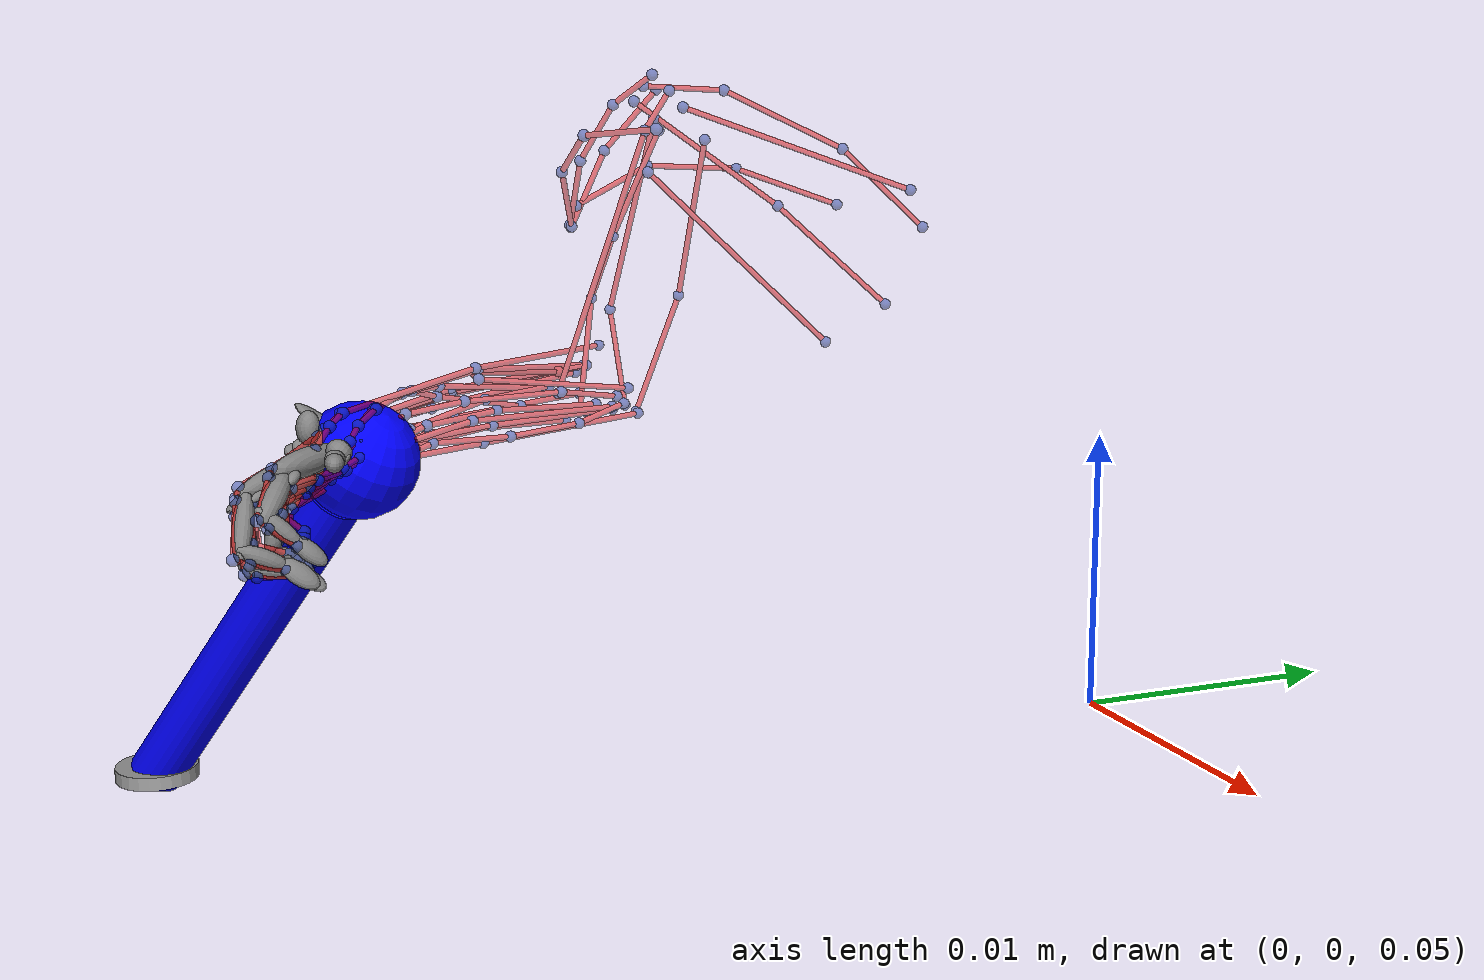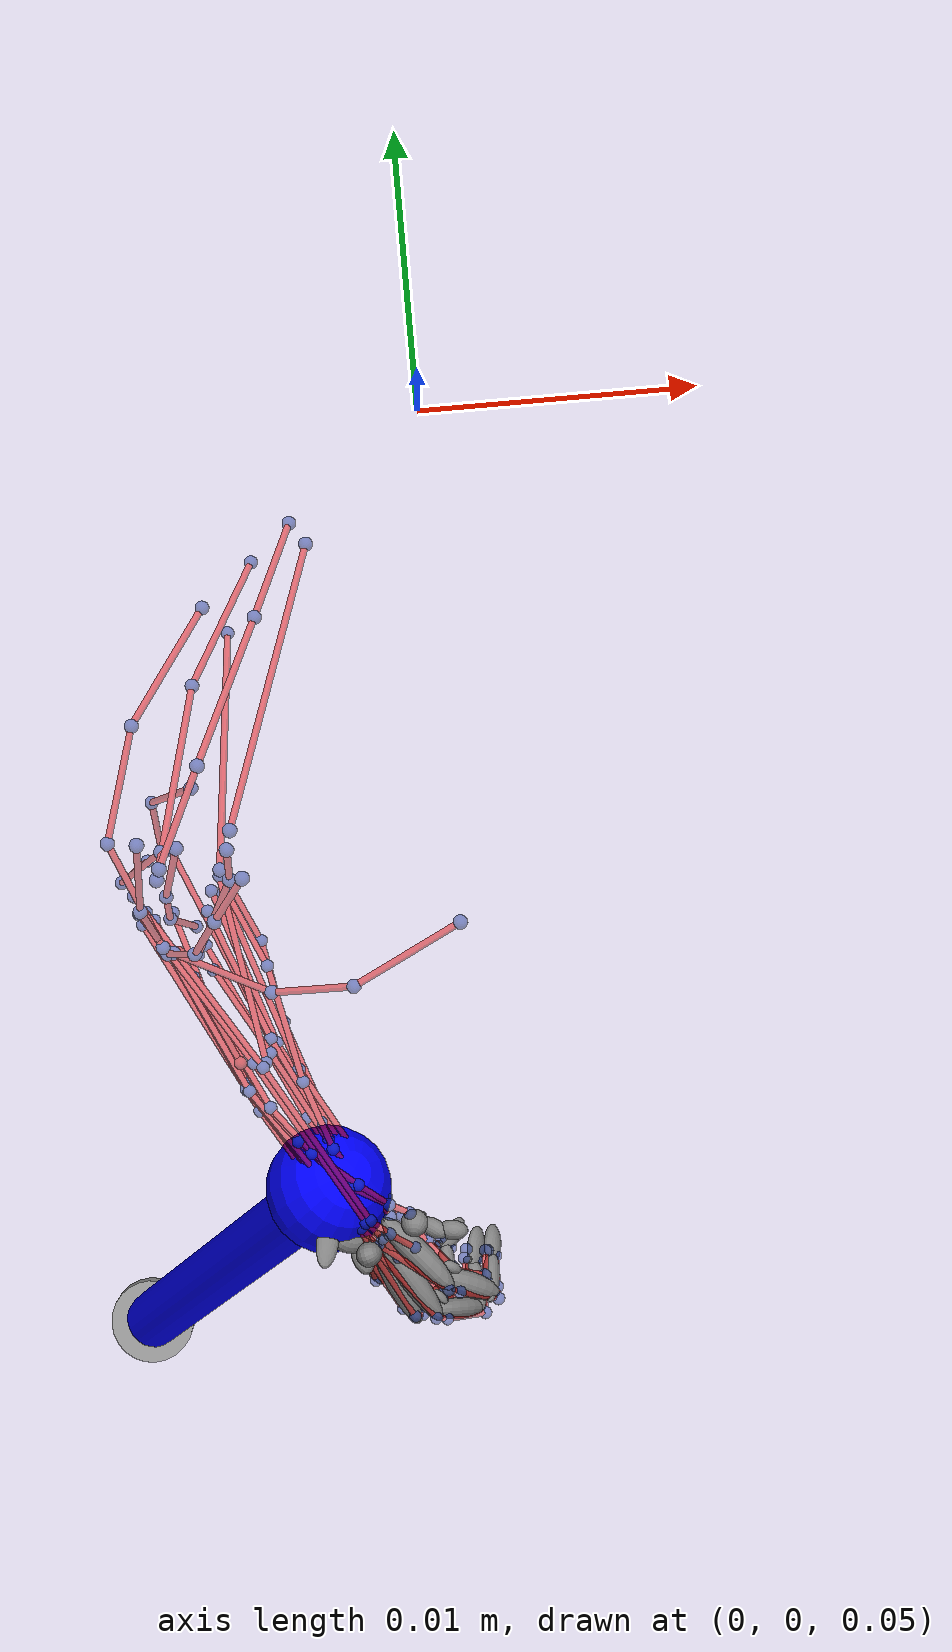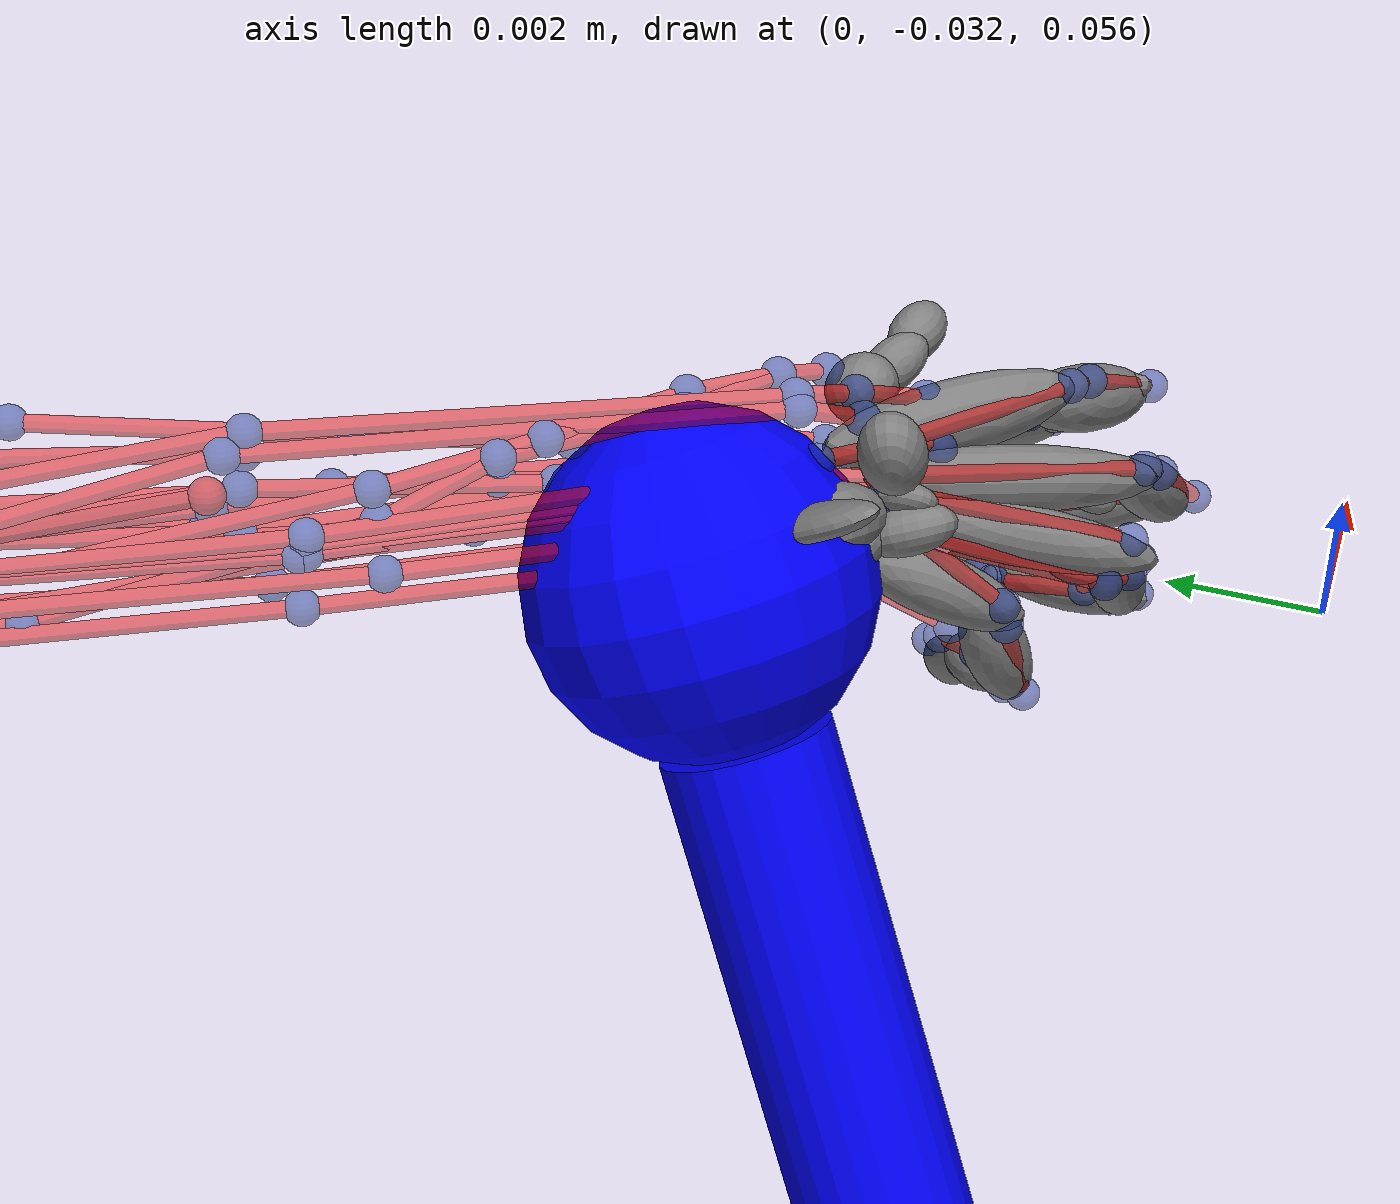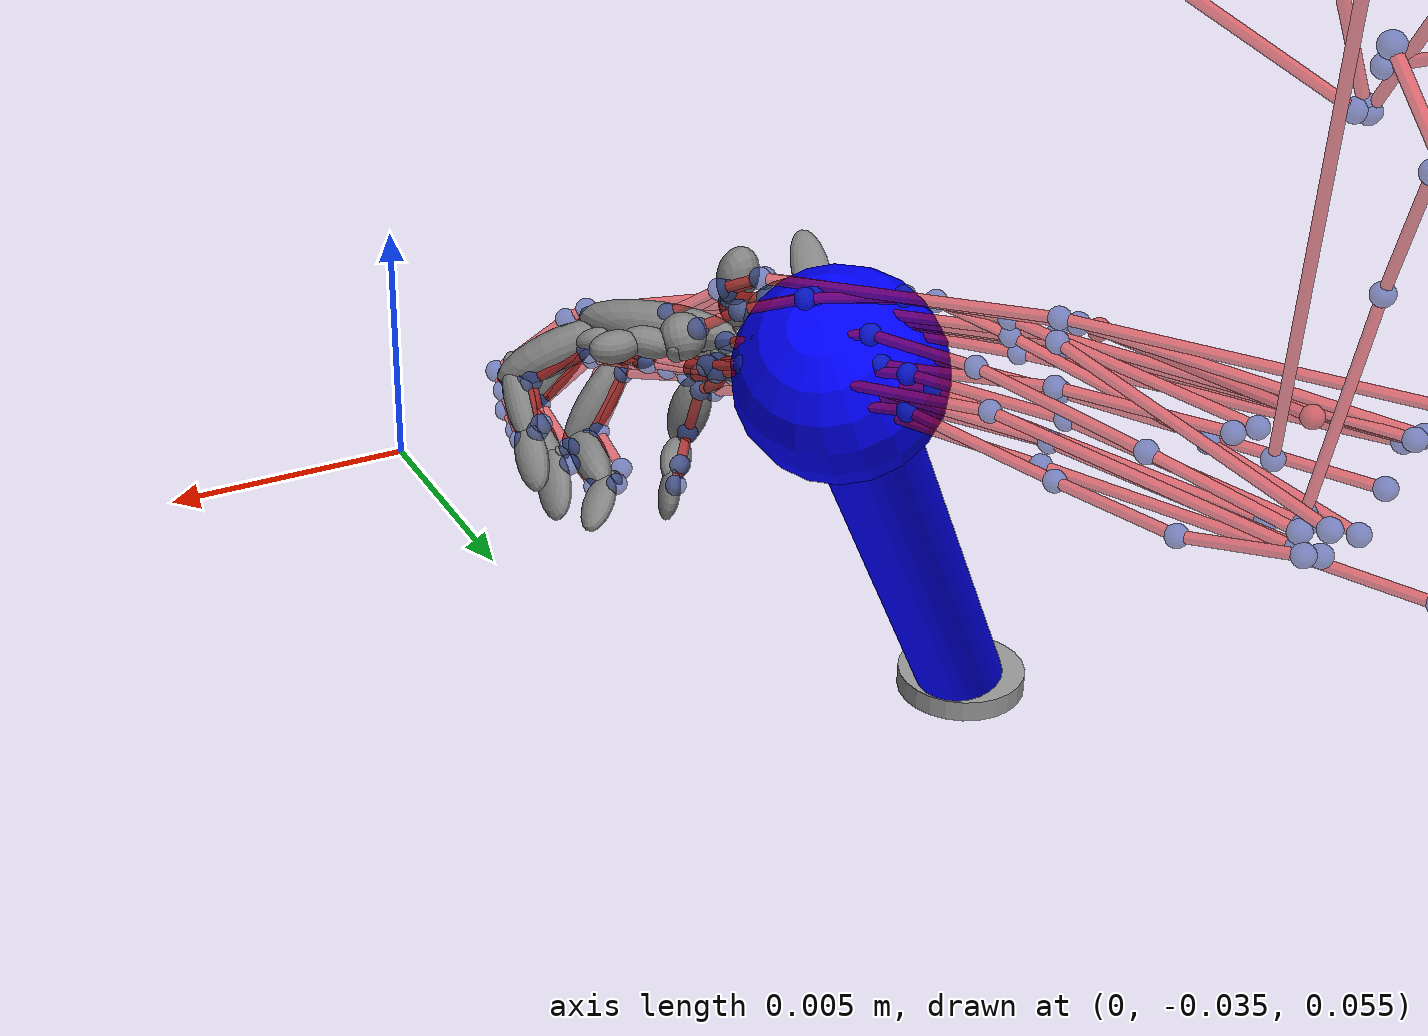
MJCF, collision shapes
<?xml version="1.0" encoding="utf-8"?>
<mujoco model="mouse_forelimb_right_hand_v22">

  <compiler angle="degree" meshdir="/root/vast/eric/janelia_model/v22"/>

  <option integrator="Euler" timestep="0.001" solver="Newton" iterations="6" ls_iterations="6"/>

  <default>
    <joint limited="true" solreflimit="0.01 1" solimplimit="0.99 0.9999 0" armature="1e-9" damping="1e-6" stiffness="1e-12"/>
    <muscle ctrllimited="true" ctrlrange="0 1"/>

    <geom contype="0" conaffinity="0"/>
    <default class="hand_visual">
      <geom contype="0" conaffinity="0"/>
    </default>
  </default>

  <size njmax="4000" nconmax="4000" nuser_jnt="1"/>

  <visual>
    <headlight diffuse=".5 .5 .5" specular="1 1 1"/>
    <global offwidth="2048" offheight="1536"/>
    <quality shadowsize="8192"/>
    <scale framelength="0.5" framewidth="0.01"/>
  </visual>

  <asset>
    <texture type="skybox" builtin="gradient" rgb1="1 1 1" rgb2="0.6 0.8 1" width="256" height="1536"/>
    <texture name="grid" type="2d" builtin="checker" width="512" height="512" rgb1=".1 .2 .3" rgb2=".2 .3 .4"/>
    <material name="grid" texture="grid" texrepeat="1 1" texuniform="true" reflectance=".2"/>
    <mesh name="clavicle_right_mesh" file="clavicle_right.stl"/>
    <mesh name="scapula_right_mesh" file="scapula_right.stl"/>
    <mesh name="humerus_right_mesh" file="humerus_right.stl"/>
    <mesh name="radius_right_mesh" file="radius_right.stl"/>
    <mesh name="ulna_right_mesh" file="ulna_right.stl"/>
    <material name="bone" specular="0.5" shininess="0.9" reflectance="0.0" rgba="0.559 0.559 0.559 1.0"/>
    <mesh name="Capitate_right_bone" file="Capitate_right_bone.obj"/>
    <mesh name="Centrale_right_bone" file="Centrale_right_bone.obj"/>
    <mesh name="Falsiformis_right_bone" file="Falsiformis_right_bone.obj"/>
    <mesh name="Hamate_right_bone" file="Hamate_right_bone.obj"/>
    <mesh name="Metacarpal_hand_1_right_bone" file="Metacarpal_hand_1_right_bone.obj"/>
    <mesh name="Metacarpal_hand_2_right_bone" file="Metacarpal_hand_2_right_bone.obj"/>
    <mesh name="Metacarpal_hand_3_right_bone" file="Metacarpal_hand_3_right_bone.obj"/>
    <mesh name="Metacarpal_hand_4_right_bone" file="Metacarpal_hand_4_right_bone.obj"/>
    <mesh name="Metacarpal_hand_5_right_bone" file="Metacarpal_hand_5_right_bone.obj"/>
    <mesh name="Multangular_right_bone" file="Multangular_right_bone.obj"/>
    <mesh name="Navicular_lunate_right_bone" file="Navicular_lunate_right_bone.obj"/>
    <mesh name="Phalanx_hand_1_1_right_bone" file="Phalanx_hand_1_1_right_bone.obj"/>
    <mesh name="Phalanx_hand_1_2_right_bone" file="Phalanx_hand_1_2_right_bone.obj"/>
    <mesh name="Phalanx_hand_1_3_right_bone" file="Phalanx_hand_1_3_right_bone.obj"/>
    <mesh name="Phalanx_hand_1_4_right_bone" file="Phalanx_hand_1_4_right_bone.obj"/>
    <mesh name="Phalanx_hand_1_5_right_bone" file="Phalanx_hand_1_5_right_bone.obj"/>
    <mesh name="Phalanx_hand_2_1_right_bone" file="Phalanx_hand_2_1_right_bone.obj"/>
    <mesh name="Phalanx_hand_2_2_right_bone" file="Phalanx_hand_2_2_right_bone.obj"/>
    <mesh name="Phalanx_hand_2_3_right_bone" file="Phalanx_hand_2_3_right_bone.obj"/>
    <mesh name="Phalanx_hand_2_4_right_bone" file="Phalanx_hand_2_4_right_bone.obj"/>
    <mesh name="Phalanx_hand_2_5_right_bone" file="Phalanx_hand_2_5_right_bone.obj"/>
    <mesh name="Phalanx_hand_3_2_right_bone" file="Phalanx_hand_3_2_right_bone.obj"/>
    <mesh name="Phalanx_hand_3_3_right_bone" file="Phalanx_hand_3_3_right_bone.obj"/>
    <mesh name="Phalanx_hand_3_4_right_bone" file="Phalanx_hand_3_4_right_bone.obj"/>
    <mesh name="Phalanx_hand_3_5_right_bone" file="Phalanx_hand_3_5_right_bone.obj"/>
    <mesh name="Pisiform_right_bone" file="Pisiform_right_bone.obj"/>
    <mesh name="Sesamoid_elbow_right_bone" file="Sesamoid_elbow_right_bone.obj"/>
    <mesh name="Sesamoid_hand_a_right_bone" file="Sesamoid_hand_a_right_bone.obj"/>
    <mesh name="Sesamoid_hand_b_right_bone" file="Sesamoid_hand_b_right_bone.obj"/>
    <mesh name="Sesamoid_hand_c_right_bone" file="Sesamoid_hand_c_right_bone.obj"/>
    <mesh name="Sesamoid_hand_d_right_bone" file="Sesamoid_hand_d_right_bone.obj"/>
    <mesh name="Sesamoid_hand_e_right_bone" file="Sesamoid_hand_e_right_bone.obj"/>
    <mesh name="Sesamoid_hand_f_right_bone" file="Sesamoid_hand_f_right_bone.obj"/>
    <mesh name="Sesamoid_hand_g_right_bone" file="Sesamoid_hand_g_right_bone.obj"/>
    <mesh name="Sesamoid_hand_h_right_bone" file="Sesamoid_hand_h_right_bone.obj"/>
    <mesh name="Sesamoid_hand_i_right_bone" file="Sesamoid_hand_i_right_bone.obj"/>
    <mesh name="Sesamoid_hand_j_right_bone" file="Sesamoid_hand_j_right_bone.obj"/>
    <mesh name="Sesamoid_hand_l_right_bone" file="Sesamoid_hand_l_right_bone.obj"/>
    <mesh name="Sesamoid_hand_m_right_bone" file="Sesamoid_hand_m_right_bone.obj"/>
    <mesh name="Triangular_right_bone" file="Triangular_right_bone.obj"/>
  </asset>

  <worldbody>
    <light directional="true"/>
    <body name="joystick_base" pos="-0.01264354 -0.03211015 0.04737563">
      <joint name="x_slide" type="slide" axis="1 0 0" limited="true" range="-0.006 0.006" damping="0.0099" stiffness="14.8"/>
      <joint name="y_slide" type="slide" axis="0 1 0" limited="true" range="-0.006 0.006" damping="0.0082" stiffness="11.2"/>
      <geom name="circular_base" type="cylinder" size="0.0015 0.00025" pos="0 0 0" rgba="0.6 0.6 0.6 1" contype="1" conaffinity="2"/>
      <body name="joystick" pos="0 0 0" quat="0.94389458 -0.21721094 0.24876180 0.00000000">
        <geom name="joystick_geom" type="cylinder" size="0.001 0.0071815" pos="0 0 0.0071815" rgba="0 0 1 1" contype="1" conaffinity="2" density="40000"/>
        <geom name="joystick_ball" type="sphere" size="0.002" pos="0 0 0.016184" rgba="0 0 1 1" contype="1" conaffinity="2"/>
      </body>
    </body>

    <body name="ground" euler="0 0 0">
      <camera name="my_camera" pos="0.04 .004 0.037" fovy="20" quat="0.6532815 0.2705981 0.2705981 0.6532815"/>
      <camera name="close-profile" pos="0.04 .004 0.037" fovy="20" quat="0.6532815 0.2705981 0.2705981 0.6532815"/>
      <camera name="janelia_cam" pos="0.020 -0.035 0.065" xyaxes="1 0 0 0 0 1" fovy="55"/>
    </body>

    <camera name="arm_joystick_fixed_view"
            pos="-0.03940696 -0.04889572 0.09061815"
            xyaxes="0.65772284 -0.75326002 0.00000000  0.46960983 0.41004846 0.78187395"
            fovy="45"/>

    <!-- Shoulder base: allows small translational movement -->
    <body name="shoulder_base" pos="0 0 0">
      <joint name="sh_tx" type="slide" axis="1 0 0" range="-0.01 0.01" damping="0.1" stiffness="10" springref="0"/>
      <joint name="sh_ty" type="slide" axis="0 1 0" range="-0.01 0.01" damping="0.1" stiffness="10" springref="0"/>
      <joint name="sh_tz" type="slide" axis="0 0 1" range="-0.01 0.01" damping="0.1" stiffness="10" springref="0"/>
      <body name="clavicle" pos="-0.00077637 -0.01474939 0.07146154" quat="0.08848527 0.63600993 -0.76341355 -0.06972465">
        <geom type="mesh" mesh="clavicle_right_mesh" density="160885.51"/>
        <site name="Pec_C_Origin" pos="0.001690 -0.000940 0.000409" rgba=".1 .2 .6 .5" size="0.0002"/>
        <site name="Pec_C_via1" pos="0.003673 0.001616 0.001337" rgba=".1 .2 .6 .5" size="0.0002"/>
        <site name="Pec_C_via2" pos="0.004120 0.003535 0.003103" rgba=".1 .2 .6 .5" size="0.0002"/>
        <site name="MD_Origin" pos="0.001004 0.005114 -0.000030" rgba=".1 .2 .6 .5" size="0.0002"/>
        <body name="scapula" pos="-0.00875153 0.00414122 0.00650980" quat="0.63900059 0.06419990 0.43511349 -0.63105696">
          <geom type="mesh" mesh="scapula_right_mesh" density="34044.87"/>
          <site name="Lat_Origin" pos="-0.002869 0.001007 0.002679" rgba=".1 .2 .6 .5" size="0.0002"/>
          <site name="AD_Origin" pos="-0.000900 0.011151 -0.001306" rgba=".1 .2 .6 .5" size="0.0002"/>
          <site name="PD_Origin" pos="-0.000817 0.003348 -0.001317" rgba=".1 .2 .6 .5" size="0.0002"/>
          <site name="PD_via1" pos="-0.002257 0.007077 -0.001192" rgba=".1 .2 .6 .5" size="0.0002"/>
          <site name="Supraspinatus_Origin" pos="0.001278 0.000565 -0.001107" rgba=".1 .2 .6 .5" size="0.0002"/>
          <site name="Supraspinatus_via1" pos="0.001502 0.004507 -0.001894" rgba=".1 .2 .6 .5" size="0.0002"/>
          <site name="Supraspinatus_via2" pos="0.000748 0.009150 -0.001748" rgba=".1 .2 .6 .5" size="0.0002"/>
          <site name="Infraspinatus_Origin" pos="-0.001268 -0.000038 0.000895" rgba=".1 .2 .6 .5" size="0.0002"/>
          <site name="Infraspinatus_via1" pos="-0.001341 0.005195 -0.000219" rgba=".1 .2 .6 .5" size="0.0002"/>
          <site name="Subscapularis_Origin" pos="0.002287 0.001786 -0.001459" rgba=".1 .2 .6 .5" size="0.0002"/>
          <site name="Triceps_Long_Origin" pos="-0.000411 0.008784 -0.000300" rgba=".1 .2 .6 .5" size="0.0002"/>
          <site name="Biceps_Long_Origin" pos="0.001163 0.010844 -0.000189" rgba=".1 .2 .6 .5" size="0.0002"/>
          <body name="humerus" pos="-0.00000000 0.01081324 0.00000000" quat="-0.37189531 -0.03516117 -0.43715933 -0.81813771">
            <joint name="sh_rotation" type="hinge" pos="0 0 0" axis="0 1 0" armature="4e-10" damping="1e-6" stiffness="0" range="-70 40" limited="true"/>
            <joint name="sh_extension" type="hinge" pos="0 0 0" axis="0 0 1" armature="4e-10" damping="1e-6" stiffness="0" range="-80 65" limited="true"/>
            <joint name="sh_elv" type="hinge" pos="0 0 0" axis="1 0 0" armature="4e-10" damping="1e-6" stiffness="0" range="-60 89" limited="true"/>
            <geom type="mesh" mesh="humerus_right_mesh" density="4085.61"/>
            <site name="Pec_C_Insertion" pos="0.001332 0.004690 0.001647" rgba=".1 .2 .6 .5" size="0.0002"/>
            <site name="Lat_Insertion" pos="-0.000684 0.002108 0.000445" rgba=".1 .2 .6 .5" size="0.0002"/>
            <site name="AD_via1" pos="0.001789 0.001936 0.000425" rgba=".1 .2 .6 .5" size="0.0002"/>
            <site name="AD_Insertion" pos="0.001492 0.004748 0.001502" rgba=".1 .2 .6 .5" size="0.0002"/>
            <site name="PD_via2" pos="0.001648 0.002286 -0.001687" rgba=".1 .2 .6 .5" size="0.0002"/>
            <site name="PD_Insertion" pos="0.001571 0.003984 0.001419" rgba=".1 .2 .6 .5" size="0.0002"/>
            <site name="MD_via1" pos="0.000343 0.000059 0.001787" rgba=".1 .2 .6 .5" size="0.0002"/>
            <site name="MD_via2" pos="0.001030 0.002253 0.002139" rgba=".1 .2 .6 .5" size="0.0002"/>
            <site name="MD_Insertion" pos="0.001497 0.004679 0.001585" rgba=".1 .2 .6 .5" size="0.0002"/>
            <site name="Supraspinatus_Insertion" pos="0.001006 -0.000647 -0.000074" rgba=".1 .2 .6 .5" size="0.0002"/>
            <site name="Infraspinatus_Insertion" pos="0.001152 -0.000047 0.000088" rgba=".1 .2 .6 .5" size="0.0002"/>
            <site name="Subscapularis_Insertion" pos="-0.001149 -0.000370 -0.000111" rgba=".1 .2 .6 .5" size="0.0002"/>
            <site name="Triceps_Lateral_Origin" pos="0.000646 0.000398 -0.000569" rgba=".1 .2 .6 .5" size="0.0002"/>
            <site name="Triceps_Lateral_via1" pos="0.001433 0.007766 -0.001157" rgba=".1 .2 .6 .5" size="0.0002"/>
            <site name="Triceps_Long_via1" pos="-0.000392 0.006639 -0.002702" rgba=".1 .2 .6 .5" size="0.0002"/>
            <site name="Triceps_Long_Insertion" pos="-0.000381 0.011173 -0.001855" rgba=".1 .2 .6 .5" size="0.0002"/>
            <site name="Brachialis_Origin" pos="0.000220 0.000737 -0.000499" rgba=".1 .2 .6 .5" size="0.0002"/>
            <site name="Brachialis_via1" pos="0.000734 0.004812 0.000128" rgba=".1 .2 .6 .5" size="0.0002"/>
            <site name="Brachialis_via2" pos="0.000740 0.007163 0.000533" rgba=".1 .2 .6 .5" size="0.0002"/>
            <site name="Biceps_Long_via1" pos="-0.000622 0.000671 0.000946" rgba=".1 .2 .6 .5" size="0.0002"/>
            <site name="extensordigitiquatri_Origin" pos="0.001321 0.010193 0.000021" rgba=".1 .2 .6 .5" size="0.0002"/>
            <site name="flexor_digitorum_profundus_UH_Origin" pos="-0.000670 0.010749 0.000565" rgba=".1 .2 .6 .5" size="0.0002"/>
            <site name="fdsA_Origin" pos="-0.001084 0.010811 0.000063" rgba=".1 .2 .6 .5" size="0.0002"/>
            <site name="extensorcarpiiulnaris_Origin" pos="0.000898 0.010869 0.000002" rgba=".1 .2 .6 .5" size="0.0002"/>
            <site name="edcD_Origin" pos="0.001077 0.009851 -0.000241" rgba=".1 .2 .6 .5" size="0.0002"/>
            <site name="pronatorteres_Origin" pos="-0.001425 0.009892 -0.000142" rgba=".1 .2 .6 .5" size="0.0002"/>
            <site name="Flexor_digitorum_profundus_SH_Origin" pos="-0.001335 0.010625 0.000347" rgba=".1 .2 .6 .5" size="0.0002"/>
            <site name="edcA_Origin" pos="0.001077 0.009851 -0.000241" rgba=".1 .2 .6 .5" size="0.0002"/>
            <site name="flexorcarpiradialis_Origin" pos="-0.001411 0.010203 0.000326" rgba=".1 .2 .6 .5" size="0.0002"/>
            <site name="fdsB_Origin" pos="-0.001084 0.010811 0.000063" rgba=".1 .2 .6 .5" size="0.0002"/>
            <site name="extensororcarpiradialisbrevis_Origin" pos="0.001290 0.009898 -0.000297" rgba=".1 .2 .6 .5" size="0.0002"/>
            <site name="edcC_Origin" pos="0.001077 0.009851 -0.000241" rgba=".1 .2 .6 .5" size="0.0002"/>
            <site name="palmarislongus_Origin" pos="-0.001628 0.010404 0.000115" rgba=".1 .2 .6 .5" size="0.0002"/>
            <site name="fdsC_Origin" pos="-0.001084 0.010811 0.000063" rgba=".1 .2 .6 .5" size="0.0002"/>
            <site name="edcB_Origin" pos="0.001077 0.009851 -0.000241" rgba=".1 .2 .6 .5" size="0.0002"/>
            <site name="extensorcarpiradialislongus_Origin" pos="0.001221 0.009099 -0.000773" rgba=".1 .2 .6 .5" size="0.0002"/>
            <body name="ulna" pos="-0.00000000 0.01036825 -0.00000000" quat="0.76125455 0.64448375 -0.05247255 -0.04877482">
              <joint name="elbow" pos="0 0 0" axis="1 0 0" armature="4e-10" damping="1e-6" stiffness="0" range="-70 80" limited="true"/>
              <geom type="mesh" mesh="ulna_right_mesh" density="6790.82"/>
              <geom name="Sesamoid_elbow_right_bone" mesh="Sesamoid_elbow_right_bone" type="mesh" material="bone" class="hand_visual" density="6790.82"/>
              <site name="Triceps_Lateral_Insertion" pos="0.000036 -0.001602 -0.001044" rgba=".1 .2 .6 .5" size="0.0002"/>
              <site name="Brachialis_Insertion" pos="-0.000247 0.000898 -0.000497" rgba=".1 .2 .6 .5" size="0.0002"/>
              <site name="extensordigitiquatri_via1" pos="0.000833 0.006794 0.000048" rgba=".1 .2 .6 .5" size="0.0002"/>
              <site name="extensordigitiquatri_via2" pos="0.000143 0.011598 0.000121" rgba=".1 .2 .6 .5" size="0.0002"/>
              <site name="flexor_digitorum_profundus_UH_via1" pos="-0.000477 0.004988 0.000285" rgba=".1 .2 .6 .5" size="0.0002"/>
              <site name="flexor_digitorum_profundus_UH_via3" pos="-0.000981 0.011160 -0.000046" rgba=".1 .2 .6 .5" size="0.0002"/>
              <site name="extensorcarpiiulnaris_via1" pos="0.000642 0.005914 -0.000394" rgba=".1 .2 .6 .5" size="0.0002"/>
              <site name="extensorcarpiiulnaris_via2" pos="0.000276 0.011171 -0.000182" rgba=".1 .2 .6 .5" size="0.0002"/>
              <site name="flexor_digitorum_profundus_MH_Origin" pos="-0.000318 0.001578 -0.000861" rgba=".1 .2 .6 .5" size="0.0002"/>
              <site name="flexor_digitorum_profundus_MH_via1" pos="-0.000401 0.007757 -0.000079" rgba=".1 .2 .6 .5" size="0.0002"/>
              <site name="flexor_digitorum_profundus_MH_via2" pos="-0.000971 0.011044 -0.000258" rgba=".1 .2 .6 .5" size="0.0002"/>
              <site name="flexorcarpiiulnaris_Origin" pos="-0.000773 -0.001553 -0.000963" rgba=".1 .2 .6 .5" size="0.0002"/>
              <site name="flexorcarpiiulnaris_via1" pos="-0.000700 0.005547 -0.000785" rgba=".1 .2 .6 .5" size="0.0002"/>
              <site name="epl_Origin" pos="0.000090 0.000204 -0.001007" rgba=".1 .2 .6 .5" size="0.0002"/>

              <site name="Supinator_Origin" pos="0.000862 0.001247 0.000484" rgba=".8 .1 .1 .6" size="0.0002"/>

              <body name="radius" pos="0 0 0">
                <joint name="forearm_supination" type="hinge" pos="0 0 0" axis="0 1 0" range="-90 90" limited="true" damping="1e-6"/>
                <geom type="mesh" mesh="radius_right_mesh" density="6790.82"/>
                <site name="Supinator_Insertion" pos="0.000903 0.005049 0.001077" rgba=".8 .1 .1 .6" size="0.0002"/>
                <site name="Biceps_Long_Insertion" pos="0.000239 0.001654 -0.000030" rgba=".1 .2 .6 .5" size="0.0002"/>
                <site name="flexor_digitorum_profundus_UH_via2" pos="-0.000622 0.008040 0.000386" rgba=".1 .2 .6 .5" size="0.0002"/>
                <site name="Flexor_digitorum_profundus_RH_Origin" pos="0.000141 0.002243 0.000419" rgba=".1 .2 .6 .5" size="0.0002"/>
                <site name="Flexor_digitorum_profundus_RH_via1" pos="-0.000176 0.005318 0.000627" rgba=".1 .2 .6 .5" size="0.0002"/>
                <site name="Flexor_digitorum_profundus_RH_via2" pos="-0.000565 0.008674 0.000337" rgba=".1 .2 .6 .5" size="0.0002"/>
                <site name="Flexor_digitorum_profundus_RH_via3" pos="-0.001173 0.011150 0.000162" rgba=".1 .2 .6 .5" size="0.0002"/>
                <site name="fdsA_via1" pos="-0.000691 0.005261 -0.000140" rgba=".1 .2 .6 .5" size="0.0002"/>
                <site name="fdsA_via2" pos="-0.000959 0.009375 0.000154" rgba=".1 .2 .6 .5" size="0.0002"/>
                <site name="fdsA_via3" pos="-0.001331 0.011088 0.000064" rgba=".1 .2 .6 .5" size="0.0002"/>
                <site name="epb_Origin" pos="0.000716 0.002172 0.000049" rgba=".1 .2 .6 .5" size="0.0002"/>
                <site name="epb_via1" pos="0.000705 0.006712 0.000971" rgba=".1 .2 .6 .5" size="0.0002"/>
                <site name="epb_via2" pos="0.000294 0.008528 0.001259" rgba=".1 .2 .6 .5" size="0.0002"/>
                <site name="epb_via3" pos="-0.000490 0.010094 0.001363" rgba=".1 .2 .6 .5" size="0.0002"/>
                <site name="epb_via4" pos="-0.001091 0.011154 0.001264" rgba=".1 .2 .6 .5" size="0.0002"/>
                <site name="edcD_via1" pos="0.000963 0.005932 0.000390" rgba=".1 .2 .6 .5" size="0.0002"/>
                <site name="edcD_via2" pos="0.000008 0.011454 0.000365" rgba=".1 .2 .6 .5" size="0.0002"/>
                <site name="pronatorteres_Insertion" pos="0.000240 0.005414 0.001240" rgba=".1 .2 .6 .5" size="0.0002"/>
                <site name="Flexor_digitorum_profundus_SH_via1" pos="-0.000804 0.006258 0.000303" rgba=".1 .2 .6 .5" size="0.0002"/>
                <site name="Flexor_digitorum_profundus_SH_via2" pos="-0.001379 0.011152 0.000231" rgba=".1 .2 .6 .5" size="0.0002"/>
                <site name="edcA_via1" pos="0.000957 0.006017 0.000585" rgba=".1 .2 .6 .5" size="0.0002"/>
                <site name="edcA_via2" pos="-0.000112 0.011451 0.000658" rgba=".1 .2 .6 .5" size="0.0002"/>
                <site name="flexorcarpiradialis_via1" pos="-0.001263 0.002884 0.001031" rgba=".1 .2 .6 .5" size="0.0002"/>
                <site name="flexorcarpiradialis_via2" pos="-0.000564 0.006545 0.000998" rgba=".1 .2 .6 .5" size="0.0002"/>
                <site name="flexorcarpiradialis_via3" pos="-0.000439 0.008838 0.000889" rgba=".1 .2 .6 .5" size="0.0002"/>
                <site name="flexorcarpiradialis_via4" pos="-0.001052 0.010916 0.000568" rgba=".1 .2 .6 .5" size="0.0002"/>
                <site name="fdsB_via1" pos="-0.000691 0.005261 -0.000140" rgba=".1 .2 .6 .5" size="0.0002"/>
                <site name="fdsB_via2" pos="-0.000926 0.009410 -0.000105" rgba=".1 .2 .6 .5" size="0.0002"/>
                <site name="fdsB_via3" pos="-0.001174 0.011068 -0.000102" rgba=".1 .2 .6 .5" size="0.0002"/>
                <site name="extensororcarpiradialisbrevis_via1" pos="0.000619 0.005215 0.001389" rgba=".1 .2 .6 .5" size="0.0002"/>
                <site name="extensororcarpiradialisbrevis_via2" pos="-0.000181 0.011260 0.001248" rgba=".1 .2 .6 .5" size="0.0002"/>
                <site name="edcC_via1" pos="0.000957 0.005992 0.000393" rgba=".1 .2 .6 .5" size="0.0002"/>
                <site name="edcC_via2" pos="0.000012 0.011376 0.000427" rgba=".1 .2 .6 .5" size="0.0002"/>
                <site name="palmarislongus_via1" pos="-0.001758 0.002233 -0.000105" rgba=".1 .2 .6 .5" size="0.0002"/>
                <site name="palmarislongus_via2" pos="-0.001254 0.004841 -0.000371" rgba=".1 .2 .6 .5" size="0.0002"/>
                <site name="palmarislongus_via3" pos="-0.000963 0.007953 -0.000142" rgba=".1 .2 .6 .5" size="0.0002"/>
                <site name="fdsC_via1" pos="-0.000691 0.005261 -0.000140" rgba=".1 .2 .6 .5" size="0.0002"/>
                <site name="fdsC_via2" pos="-0.000781 0.009400 -0.000147" rgba=".1 .2 .6 .5" size="0.0002"/>
                <site name="fdsC_via3" pos="-0.001092 0.011043 -0.000205" rgba=".1 .2 .6 .5" size="0.0002"/>
                <site name="edcB_via1" pos="0.000945 0.005983 0.000460" rgba=".1 .2 .6 .5" size="0.0002"/>
                <site name="edcB_via2" pos="-0.000030 0.011400 0.000499" rgba=".1 .2 .6 .5" size="0.0002"/>
                <site name="epl_via1" pos="0.000554 0.003046 -0.000450" rgba=".1 .2 .6 .5" size="0.0002"/>
                <site name="epl_via2" pos="0.000684 0.006759 0.000580" rgba=".1 .2 .6 .5" size="0.0002"/>
                <site name="epl_via3" pos="0.000475 0.008021 0.001151" rgba=".1 .2 .6 .5" size="0.0002"/>
                <site name="epl_via4" pos="-0.000262 0.010047 0.001260" rgba=".1 .2 .6 .5" size="0.0002"/>
                <site name="epl_via5" pos="-0.001091 0.011154 0.001264" rgba=".1 .2 .6 .5" size="0.0002"/>
                <site name="extensorcarpiradialislongus_via1" pos="0.000466 0.005447 0.001568" rgba=".1 .2 .6 .5" size="0.0002"/>
                <site name="extensorcarpiradialislongus_via2" pos="-0.000310 0.011245 0.001351" rgba=".1 .2 .6 .5" size="0.0002"/>

              <body name="wrist" pos="-0.00000000 0.01151812 0.00000000" quat="0.98713225 -0.13814126 0.06379110 0.04916923">
                <joint name="wrist_flexion" type="hinge" pos="0 0 0" axis="1 0 0" range="-60 60" limited="true" damping="1e-6"/>
                <joint name="rz_N_L_C_right" type="hinge" pos="0 0 0" axis="0 0 1" range="-15 15" limited="true" damping="1e-6"/>
                <geom name="Navicular_lunate_right_bone" type="mesh" mesh="Navicular_lunate_right_bone" material="bone" class="hand_visual" density="58706.12" contype="0" conaffinity="0"/>
                <geom name="Navicular_lunate_right_bone_col" type="ellipsoid" size="0.0007837002066744987 0.0005535501809453107 0.00042048250907100737" pos="0.0002297458704560995 -4.610605537891388e-05 0.00012871623039245605" quat="0.4281717538833618 -0.1286843866109848 -0.24640299379825592 0.8598807454109192" contype="2" conaffinity="1" group="1"/>
                <geom name="Pisiform_right_bone" type="mesh" mesh="Pisiform_right_bone" material="bone" class="hand_visual" density="58706.12" contype="0" conaffinity="0"/>
                <geom name="Pisiform_right_bone_col" type="ellipsoid" size="0.0005648015066981316 0.00038427120307460427 0.0003945605712942779" pos="3.2865675166249275e-05 0.00047325482591986656 0.0009732461767271161" quat="0.23534496128559113 -0.539776086807251 -0.1000983864068985 0.8020195960998535" contype="2" conaffinity="1" group="1"/>
                <geom name="Triangular_right_bone" type="mesh" mesh="Triangular_right_bone" material="bone" class="hand_visual" density="58706.12" contype="0" conaffinity="0"/>
                <geom name="Triangular_right_bone_col" type="ellipsoid" size="0.00043076969282311584 0.0003334793456300743 0.0002056218164034852" pos="-4.382221959531307e-05 0.0007932311855256557 0.0003795623779296875" quat="0.3190799653530121 0.31977325677871704 -0.1943703442811966 -0.8707199692726135" contype="2" conaffinity="1" group="1"/>
                <geom name="Hamate_right_bone" type="mesh" mesh="Hamate_right_bone" material="bone" class="hand_visual" density="58706.12" contype="0" conaffinity="0"/>
                <geom name="Hamate_right_bone_col" type="ellipsoid" size="0.0005550822917126247 0.00035245631388552967 0.00029014749452471733" pos="0.00018586660735309124 0.0008974582888185978 0.00015377893578261137" quat="0.001709582982584834 0.7789673209190369 0.5266167521476746 0.34041425585746765" contype="2" conaffinity="1" group="1"/>
                <geom name="Falsiformis_right_bone" type="mesh" mesh="Falsiformis_right_bone" material="bone" class="hand_visual" density="58706.12" contype="0" conaffinity="0"/>
                <geom name="Falsiformis_right_bone_col" type="ellipsoid" size="0.0008822327059055529 0.0003524172741740123 0.00017914276678884095" pos="0.0008809349965304136 -0.0004411204718053341 0.000490794307552278" quat="0.8759335279464722 0.23272056877613068 -0.2873495817184448 0.3098577558994293" contype="2" conaffinity="1" group="1"/>
                <geom name="Centrale_right_bone" type="mesh" mesh="Centrale_right_bone" material="bone" class="hand_visual" density="58706.12" contype="0" conaffinity="0"/>
                <geom name="Centrale_right_bone_col" type="ellipsoid" size="0.00040196315249097295 0.000333645150155798 0.00015634482840042561" pos="0.00014722743071615696 5.789753049612045e-05 -0.0002170155057683587" quat="0.31908726692199707 -0.18404355645179749 -0.47482815384864807 0.7992806434631348" contype="2" conaffinity="1" group="1"/>
                <geom name="Capitate_right_bone" type="mesh" mesh="Capitate_right_bone" material="bone" class="hand_visual" density="58706.12" contype="0" conaffinity="0"/>
                <geom name="Capitate_right_bone_col" type="ellipsoid" size="0.00043159346289744355 0.00027813212437872645 0.0003330964915729418" pos="0.00011332053691148758 0.00043739378452301025 -0.0001642454881221056" quat="0.1440650373697281 -0.34502601623535156 0.20520639419555664 0.904484748840332" contype="2" conaffinity="1" group="1"/>
                <site name="extensordigitiquatri_via3" pos="0.000076 0.000688 0.000043" rgba=".1 .2 .6 .5" size="0.0002"/>
                <site name="flexor_digitorum_profundus_UH_via4" pos="-0.000930 0.000745 -0.000339" rgba=".1 .2 .6 .5" size="0.0002"/>
                <site name="Flexor_digitorum_profundus_RH_via4" pos="-0.001171 0.000648 -0.000136" rgba=".1 .2 .6 .5" size="0.0002"/>
                <site name="fdsA_via4" pos="-0.001505 0.000398 -0.000122" rgba=".1 .2 .6 .5" size="0.0002"/>
                <site name="edcD_via3" pos="-0.000027 0.000636 0.000219" rgba=".1 .2 .6 .5" size="0.0002"/>
                <site name="Abductor_digiti_quinti_hand_Origin" pos="-0.000896 -0.000106 -0.000863" rgba=".1 .2 .6 .5" size="0.0002"/>
                <site name="Flexor_digitorum_profundus_SH_via3" pos="-0.001540 0.000514 0.000037" rgba=".1 .2 .6 .5" size="0.0002"/>
                <site name="edcA_via3" pos="-0.000385 0.000487 0.000789" rgba=".1 .2 .6 .5" size="0.0002"/>
                <site name="flexorcarpiradialis_via5" pos="-0.001182 0.000197 0.000293" rgba=".1 .2 .6 .5" size="0.0002"/>
                <site name="flexor_digitorum_profundus_MH_via3" pos="-0.000893 0.000640 -0.000590" rgba=".1 .2 .6 .5" size="0.0002"/>
                <site name="fdsB_via4" pos="-0.001212 0.000366 -0.000250" rgba=".1 .2 .6 .5" size="0.0002"/>
                <site name="extensororcarpiradialisbrevis_via3" pos="-0.000570 0.000256 0.001014" rgba=".1 .2 .6 .5" size="0.0002"/>
                <site name="flexorcarpiiulnaris_Insertion" pos="-0.000903 -0.000570 -0.000771" rgba=".1 .2 .6 .5" size="0.0002"/>
                <site name="edcC_via3" pos="-0.000127 0.000574 0.000422" rgba=".1 .2 .6 .5" size="0.0002"/>
                <site name="palmarislongus_Insertion" pos="-0.001516 -0.000549 -0.000649" rgba=".1 .2 .6 .5" size="0.0002"/>
                <site name="fdsC_via4" pos="-0.001071 0.000378 -0.000419" rgba=".1 .2 .6 .5" size="0.0002"/>
                <site name="edcB_via3" pos="-0.000213 0.000569 0.000543" rgba=".1 .2 .6 .5" size="0.0002"/>
                <site name="extensorcarpiradialislongus_via3" pos="-0.000811 0.000182 0.001178" rgba=".1 .2 .6 .5" size="0.0002"/>
                <body name="Metacarpal_hand_1_right" pos="-0.00128667 0.00037813 0.00083782" quat="0.86944604 -0.06482355 0.14071660 0.46910563">
                  <geom name="Sesamoid_hand_b_right_bone" mesh="Sesamoid_hand_b_right_bone" type="mesh" material="bone" group="0" class="hand_visual" contype="0" conaffinity="0"/>
              <geom name="Sesamoid_hand_b_right_bone_col" type="ellipsoid" size="0.00028224807465448976 0.00018110145174432546 0.00011936548980884254" pos="-7.9834193456918e-05 0.000704567413777113 -0.00031446036882698536" quat="0.15466925501823425 -0.9549859166145325 0.09436117857694626 0.23489423096179962" contype="2" conaffinity="1" group="1"/>
                  <geom name="Multangular_right_bone" mesh="Multangular_right_bone" type="mesh" material="bone" group="0" class="hand_visual"/>
                  <geom name="Metacarpal_hand_1_right_bone" mesh="Metacarpal_hand_1_right_bone" type="mesh" material="bone" group="0" class="hand_visual" contype="0" conaffinity="0"/>
              <geom name="Metacarpal_hand_1_right_bone_col" type="ellipsoid" size="0.00042687358650361426 0.0003952798017824669 0.0004364557513196962" pos="-1.5615893062204123e-05 0.00045968801714479923 -9.042967576533556e-05" quat="0.680575966835022 0.22539953887462616 -0.0028835791163146496 0.6971392035484314" contype="2" conaffinity="1" group="1"/>
                  <site name="epb_Insertion" pos="-0.000433 0.000213 -0.000071" rgba=".1 .2 .6 .5" size="0.0002"/>
                  <site name="epl_Insertion" pos="-0.000433 0.000213 -0.000071" rgba=".1 .2 .6 .5" size="0.0002"/>
                  <body name="Phalanx_hand_1_1_right" pos="-0.00000000 0.00067536 -0.00000000" quat="0.94125921 0.25909334 0.20487878 -0.07019016">
                    <joint name="rx_Phalanx_hand_1_1_right" type="hinge" limited="true" pos="0.0 0.0 0.0" axis="1.0 0.0 0.0" range="-20 90" stiffness="0"/>
                    <joint name="rz_Phalanx_hand_1_1_right" type="hinge" pos="0 0 0" axis="0 0 1" range="-20 20" limited="true" damping="1e-6"/>
                    <geom name="Phalanx_hand_1_1_right_bone" mesh="Phalanx_hand_1_1_right_bone" type="mesh" material="bone" group="0" class="hand_visual" contype="0" conaffinity="0"/>
              <geom name="Phalanx_hand_1_1_right_bone_col" type="ellipsoid" size="0.0004890728164523989 0.0002894149565092381 0.0002865710854933201" pos="2.362125087529421e-05 0.00037310586776584387 -9.707867866382003e-05" quat="0.0007928490522317588 0.7602683305740356 -0.6438658237457275 -0.08618699759244919" contype="2" conaffinity="1" group="1"/>

                    <body name="Phalanx_hand_2_1_right" pos="-0.00000000 0.00065974 -0.00000000" quat="0.97004509 -0.22801436 0.06510796 0.05275321">
                      <joint name="rx_Phalanx_hand_2_1_right" type="hinge" limited="true" pos="0.0 0.0 0.0" axis="1.0 0.0 0.0" range="0 100" stiffness="0"/>
                      <geom name="Phalanx_hand_2_1_right_bone" mesh="Phalanx_hand_2_1_right_bone" type="mesh" material="bone" group="0" class="hand_visual" contype="0" conaffinity="0"/>
              <geom name="Phalanx_hand_2_1_right_bone_col" type="ellipsoid" size="0.0004723376187030226 0.0003070329332234296 0.0002973566525041535" pos="-5.429997690953314e-05 0.00038592598866671324 -0.00010568481957307085" quat="0.42766979336738586 -0.5936122536659241 0.609771728515625 -0.3047974109649658" contype="2" conaffinity="1" group="1"/>

                    </body>
                  </body>
                </body>
                <body name="Metacarpal_hand_2_right" pos="-0.00103771 0.00035327 0.00068541" quat="0.96644253 0.05902667 0.20537452 0.14256865">
                  <geom name="Sesamoid_hand_i_right_bone" mesh="Sesamoid_hand_i_right_bone" type="mesh" material="bone" group="0" class="hand_visual" contype="0" conaffinity="0"/>
              <geom name="Sesamoid_hand_i_right_bone_col" type="ellipsoid" size="0.00031377148116007447 0.00015244541282299906 0.0001483732194174081" pos="5.9313373640179634e-05 0.0022535002790391445 -0.00035552226472646" quat="0.19370004534721375 0.6282374262809753 -0.7533749341964722 -0.01493673026561737" contype="2" conaffinity="1" group="1"/>
                  <geom name="Sesamoid_hand_j_right_bone" mesh="Sesamoid_hand_j_right_bone" type="mesh" material="bone" group="0" class="hand_visual" contype="0" conaffinity="0"/>
              <geom name="Sesamoid_hand_j_right_bone_col" type="ellipsoid" size="0.00033533090027049184 0.00018532914691604674 0.0001690189092187211" pos="-0.0002787270350381732 0.002366719301789999 -0.00022314538364298642" quat="0.15493755042552948 -0.745619535446167 0.5683216452598572 -0.31153786182403564" contype="2" conaffinity="1" group="1"/>
                  <geom name="Metacarpal_hand_2_right_bone" mesh="Metacarpal_hand_2_right_bone" type="mesh" material="bone" group="0" class="hand_visual" contype="0" conaffinity="0"/>
              <geom name="Metacarpal_hand_2_right_bone_col" type="ellipsoid" size="0.0015806542942300439 0.0004525682370708165 0.00042344955727458" pos="0.0001064968528226018 0.0012260102666914463 -7.521778752561659e-05" quat="0.36755508184432983 0.6170336604118347 -0.5355806946754456 -0.44421395659446716" contype="2" conaffinity="1" group="1"/>
                  <site name="fdsA_via5" pos="-0.000144 0.001351 -0.000720" rgba=".1 .2 .6 .5" size="0.0002"/>
                  <site name="edcA_via4" pos="0.000120 0.002662 0.000276" rgba=".1 .2 .6 .5" size="0.0002"/>
                  <site name="extensorcarpiradialislongus_Insertion" pos="-0.000082 0.000903 0.000145" rgba=".1 .2 .6 .5" size="0.0002"/>
                  <body name="Phalanx_hand_1_2_right" pos="-0.00000000 0.00252649 -0.00000000" quat="0.97027695 -0.22301582 0.01391076 0.09291495">
                    <joint name="rx_Phalanx_hand_1_2_right" type="hinge" limited="true" pos="0.0 0.0 0.0" axis="1.0 0.0 0.0" range="-20 90" stiffness="0"/>
                    <joint name="rz_Phalanx_hand_1_2_right" type="hinge" pos="0 0 0" axis="0 0 1" range="-20 20" limited="true" damping="1e-6"/>
                    <geom name="Phalanx_hand_1_2_right_bone" mesh="Phalanx_hand_1_2_right_bone" type="mesh" material="bone" group="0" class="hand_visual" contype="0" conaffinity="0"/>
              <geom name="Phalanx_hand_1_2_right_bone_col" type="ellipsoid" size="0.0012017625759375705 0.00040305747248482737 0.00039855595285100825" pos="4.0284241549670696e-05 0.0009321807301603258 -9.783290443010628e-05" quat="0.18915759027004242 0.6838018298149109 -0.6683969497680664 -0.2233382612466812" contype="2" conaffinity="1" group="1"/>
                    <site name="fdsA_via6" pos="-0.000131 0.000252 -0.000444" rgba=".1 .2 .6 .5" size="0.0002"/>
                    <site name="Flexor_digitorum_profundus_SH_via4" pos="-0.000125 0.000258 -0.000351" rgba=".1 .2 .6 .5" size="0.0002"/>
                    <site name="edcA_via5" pos="0.000083 0.000408 0.000324" rgba=".1 .2 .6 .5" size="0.0002"/>
                    <site name="edcA_via6" pos="0.000076 0.002082 0.000138" rgba=".1 .2 .6 .5" size="0.0002"/>
                    <body name="Phalanx_hand_2_2_right" pos="-0.00000000 0.00193517 -0.00000000" quat="0.69045466 -0.70045555 0.16852748 0.06506267">
                      <joint name="rx_Phalanx_hand_2_2_right" type="hinge" limited="true" pos="0.0 0.0 0.0" axis="1.0 0.0 0.0" range="0 100" stiffness="0"/>
                      <geom name="Phalanx_hand_2_2_right_bone" mesh="Phalanx_hand_2_2_right_bone" type="mesh" material="bone" group="0" class="hand_visual" contype="0" conaffinity="0"/>
              <geom name="Phalanx_hand_2_2_right_bone_col" type="ellipsoid" size="0.0009212680226915321 0.0002642836455923406 0.00030080823879528006" pos="4.9569018301554024e-05 0.0005441022804006934 -8.568500925321132e-05" quat="0.0362146720290184 -0.7081072330474854 0.7009227275848389 0.07733014225959778" contype="2" conaffinity="1" group="1"/>
                      <site name="fdsA_Insertion" pos="0.000051 0.000313 -0.000299" rgba=".1 .2 .6 .5" size="0.0002"/>
                      <site name="Flexor_digitorum_profundus_SH_via5" pos="-0.000023 0.000444 -0.000484" rgba=".1 .2 .6 .5" size="0.0002"/>
                      <site name="edcA_via7" pos="0.000033 0.000257 0.000166" rgba=".1 .2 .6 .5" size="0.0002"/>
                      <body name="Phalanx_hand_3_2_right" pos="0.00000000 0.00127175 0.00000000" quat="0.99221313 0.12442344 0.00536170 0.00178403">
                        <geom name="Phalanx_hand_3_2_right_bone" mesh="Phalanx_hand_3_2_right_bone" type="mesh" material="bone" group="0" class="hand_visual" contype="0" conaffinity="0"/>
              <geom name="Phalanx_hand_3_2_right_bone_col" type="ellipsoid" size="0.0007001164485700428 0.00033376887927056426 0.00021890449289253128" pos="2.4586101062595844e-05 0.0004342776956036687 -1.7543545254739e-05" quat="0.45697641372680664 -0.5240138173103333 -0.4797261357307434 0.5352055430412292" contype="2" conaffinity="1" group="1"/>
                        <site name="Flexor_digitorum_profundus_SH_via6" pos="-0.000034 -0.000068 -0.000365" rgba=".1 .2 .6 .5" size="0.0002"/>
                        <site name="Flexor_digitorum_profundus_SH_Insertion" pos="-0.000012 0.000019 -0.000250" rgba=".1 .2 .6 .5" size="0.0002"/>
                        <site name="edcA_Insertion" pos="0.000013 0.000078 0.000172" rgba=".1 .2 .6 .5" size="0.0002"/>
                      </body>
                    </body>
                  </body>
                </body>
                <body name="Metacarpal_hand_3_right" pos="-0.00063941 0.00080777 0.00033305" quat="0.96103567 0.01937197 0.26781228 0.06566295">
                  <geom name="Sesamoid_hand_g_right_bone" mesh="Sesamoid_hand_g_right_bone" type="mesh" material="bone" group="0" class="hand_visual" contype="0" conaffinity="0"/>
              <geom name="Sesamoid_hand_g_right_bone_col" type="ellipsoid" size="0.0003092387050855905 0.00016959277854766697 0.00013600068632513285" pos="0.00012514495756477118 0.0026757046580314636 -0.0002694439026527107" quat="0.22573617100715637 0.6453444957733154 -0.7244195342063904 -0.08825359493494034" contype="2" conaffinity="1" group="1"/>
                  <geom name="Sesamoid_hand_h_right_bone" mesh="Sesamoid_hand_h_right_bone" type="mesh" material="bone" group="0" class="hand_visual" contype="0" conaffinity="0"/>
              <geom name="Sesamoid_hand_h_right_bone_col" type="ellipsoid" size="0.00031314865918830037 0.00014781206846237183 0.00010825449862750247" pos="-0.00025494559668004513 0.002713883062824607 -0.000144079647725448" quat="0.6169880628585815 0.3989422619342804 -0.3991204798221588 -0.548517107963562" contype="2" conaffinity="1" group="1"/>
                  <geom name="Metacarpal_hand_3_right_bone" mesh="Metacarpal_hand_3_right_bone" type="mesh" material="bone" group="0" class="hand_visual" contype="0" conaffinity="0"/>
              <geom name="Metacarpal_hand_3_right_bone_col" type="ellipsoid" size="0.00179077860469945 0.00039994822471087904 0.0003831295242809774" pos="4.598591476678848e-05 0.0015024468302726746 5.5873359087854624e-05" quat="0.5486711859703064 0.4445313811302185 -0.4034237563610077 -0.5818943381309509" contype="2" conaffinity="1" group="1"/>
                  <site name="flexorcarpiradialis_Insertion" pos="-0.000148 0.000266 -0.000275" rgba=".1 .2 .6 .5" size="0.0002"/>
                  <site name="fdsB_via5" pos="-0.000250 0.000969 -0.000731" rgba=".1 .2 .6 .5" size="0.0002"/>
                  <site name="extensororcarpiradialisbrevis_Insertion" pos="-0.000190 0.000543 0.000265" rgba=".1 .2 .6 .5" size="0.0002"/>
                  <site name="edcB_via4" pos="0.000045 0.003013 0.000383" rgba=".1 .2 .6 .5" size="0.0002"/>
                  <body name="Phalanx_hand_1_3_right" pos="-0.00000000 0.00299405 -0.00000000" quat="0.91133559 -0.38537866 0.11947534 0.08170896">
                    <joint name="rx_Phalanx_hand_1_3_right" type="hinge" limited="true" pos="0.0 0.0 0.0" axis="1.0 0.0 0.0" range="-20 90" stiffness="0"/>
                    <joint name="rz_Phalanx_hand_1_3_right" type="hinge" pos="0 0 0" axis="0 0 1" range="-20 20" limited="true" damping="1e-6"/>
                    <geom name="Phalanx_hand_1_3_right_bone" mesh="Phalanx_hand_1_3_right_bone" type="mesh" material="bone" group="0" class="hand_visual" contype="0" conaffinity="0"/>
              <geom name="Phalanx_hand_1_3_right_bone_col" type="ellipsoid" size="0.0012912593102810607 0.0003662501694634557 0.00033117672453952633" pos="2.2149819415062666e-05 0.0010177417425438762 1.2079690350219607e-05" quat="0.05697768181562424 0.688938319683075 -0.7203633189201355 -0.056517984718084335" contype="2" conaffinity="1" group="1"/>
                    <site name="Flexor_digitorum_profundus_RH_via5" pos="0.000004 0.000242 -0.000329" rgba=".1 .2 .6 .5" size="0.0002"/>
                    <site name="fdsB_via6" pos="-0.000012 0.000228 -0.000471" rgba=".1 .2 .6 .5" size="0.0002"/>
                    <site name="edcB_via5" pos="-0.000056 0.000257 0.000330" rgba=".1 .2 .6 .5" size="0.0002"/>
                    <site name="edcB_via6" pos="0.000040 0.002249 0.000234" rgba=".1 .2 .6 .5" size="0.0002"/>
                    <body name="Phalanx_hand_2_3_right" pos="-0.00000000 0.00212166 -0.00000000" quat="0.68292081 -0.72894341 -0.01744963 0.04422784">
                      <joint name="rx_Phalanx_hand_2_3_right" type="hinge" limited="true" pos="0.0 0.0 0.0" axis="1.0 0.0 0.0" range="0 100" stiffness="0"/>
                      <geom name="Sesamoid_hand_m_right_bone" mesh="Sesamoid_hand_m_right_bone" type="mesh" material="bone" group="0" class="hand_visual" contype="0" conaffinity="0"/>
              <geom name="Sesamoid_hand_m_right_bone_col" type="ellipsoid" size="0.00018040102440863848 0.0001258305856026709 7.37344307708554e-05" pos="-9.231735020875931e-08 0.0014927831944078207 -0.0002218644949607551" quat="0.06503324955701828 0.020850230008363724 -0.9829123020172119 -0.17093674838542938" contype="2" conaffinity="1" group="1"/>
                      <geom name="Phalanx_hand_2_3_right_bone" mesh="Phalanx_hand_2_3_right_bone" type="mesh" material="bone" group="0" class="hand_visual" contype="0" conaffinity="0"/>
              <geom name="Phalanx_hand_2_3_right_bone_col" type="ellipsoid" size="0.0009257117696189129 0.00031202269019559026 0.00031127239344641566" pos="1.1133553925901651e-05 0.0007062417571432889 -7.768173236399889e-05" quat="0.742036759853363 0.021185599267482758 -0.08609245717525482 0.6644703149795532" contype="2" conaffinity="1" group="1"/>
                      <site name="Flexor_digitorum_profundus_RH_via6" pos="-0.000039 0.000348 -0.000505" rgba=".1 .2 .6 .5" size="0.0002"/>
                      <site name="fdsB_Insertion" pos="-0.000009 0.000293 -0.000309" rgba=".1 .2 .6 .5" size="0.0002"/>
                      <site name="edcB_via7" pos="0.000042 0.000278 0.000195" rgba=".1 .2 .6 .5" size="0.0002"/>
                      <body name="Phalanx_hand_3_3_right" pos="0.00000000 0.00145908 0.00000000" quat="0.96499377 0.26023817 0.03198392 -0.00633682">
                        <geom name="Phalanx_hand_3_3_right_bone" mesh="Phalanx_hand_3_3_right_bone" type="mesh" material="bone" group="0" class="hand_visual" contype="0" conaffinity="0"/>
              <geom name="Phalanx_hand_3_3_right_bone_col" type="ellipsoid" size="0.0007360045700133475 0.00038062362000346184 0.00021192220063045476" pos="-3.013497916981578e-06 0.00047844331129454076 5.2151037380099297e-05" quat="0.5355066061019897 -0.4696522057056427 -0.4554412364959717 0.5340720415115356" contype="2" conaffinity="1" group="1"/>
                        <site name="Flexor_digitorum_profundus_RH_via7" pos="0.000010 -0.000105 -0.000372" rgba=".1 .2 .6 .5" size="0.0002"/>
                        <site name="Flexor_digitorum_profundus_RH_Insertion" pos="0.000003 0.000223 -0.000340" rgba=".1 .2 .6 .5" size="0.0002"/>
                        <site name="edcB_Insertion" pos="0.000013 0.000086 0.000189" rgba=".1 .2 .6 .5" size="0.0002"/>
                      </body>
                    </body>
                  </body>
                </body>
                <body name="Metacarpal_hand_4_right" pos="-0.00029393 0.00089569 0.00010532" quat="0.85364336 -0.05341774 0.51809978 -0.00345704">
                  <geom name="Sesamoid_hand_a_right_bone" mesh="Sesamoid_hand_a_right_bone" type="mesh" material="bone" group="0" class="hand_visual" contype="0" conaffinity="0"/>
              <geom name="Sesamoid_hand_a_right_bone_col" type="ellipsoid" size="0.0002717851020861417 0.00016667410091031343 9.293900075135753e-05" pos="0.0001344872871413827 5.636061541736126e-05 -0.0005181042943149805" quat="0.08273156732320786 -0.9305413365364075 0.3514679968357086 -0.06097929924726486" contype="2" conaffinity="1" group="1"/>
                  <geom name="Sesamoid_hand_e_right_bone" mesh="Sesamoid_hand_e_right_bone" type="mesh" material="bone" group="0" class="hand_visual" contype="0" conaffinity="0"/>
              <geom name="Sesamoid_hand_e_right_bone_col" type="ellipsoid" size="0.00032886676490306854 0.00015652482397854328 0.00012442500155884773" pos="0.000274197431281209 0.002433938905596733 -0.00014898693189024925" quat="0.43480992317199707 0.544857382774353 -0.5529264807701111 -0.4564485549926758" contype="2" conaffinity="1" group="1"/>
                  <geom name="Sesamoid_hand_f_right_bone" mesh="Sesamoid_hand_f_right_bone" type="mesh" material="bone" group="0" class="hand_visual" contype="0" conaffinity="0"/>
              <geom name="Sesamoid_hand_f_right_bone_col" type="ellipsoid" size="0.0003217674093320966 0.00015718824579380453 0.00013718147238250822" pos="-0.00012271851301193237 0.002397203352302313 -0.0002887693699449301" quat="0.10266119986772537 -0.7127342820167542 0.63322514295578 -0.28372111916542053" contype="2" conaffinity="1" group="1"/>
                  <geom name="Metacarpal_hand_4_right_bone" mesh="Metacarpal_hand_4_right_bone" type="mesh" material="bone" group="0" class="hand_visual" contype="0" conaffinity="0"/>
              <geom name="Metacarpal_hand_4_right_bone_col" type="ellipsoid" size="0.001748770708218217 0.0003569774697004917 0.0003660670626969807" pos="-1.5988829545676708e-05 0.001551798195578158 4.069879651069641e-05" quat="0.22065873444080353 -0.6817464232444763 0.6809173226356506 -0.15127183496952057" contype="2" conaffinity="1" group="1"/>
                  <site name="extensordigitiquatri_via4" pos="0.000309 0.002681 0.000188" rgba=".1 .2 .6 .5" size="0.0002"/>
                  <site name="edcC_via4" pos="-0.000234 0.002801 0.000314" rgba=".1 .2 .6 .5" size="0.0002"/>
                  <site name="fdsC_via5" pos="0.000140 0.000900 -0.000822" rgba=".1 .2 .6 .5" size="0.0002"/>
                  <body name="Phalanx_hand_1_4_right" pos="0.00000000 0.00273840 -0.00000000" quat="0.88430160 -0.44540060 -0.12204157 -0.06880952">
                    <joint name="rx_Phalanx_hand_1_4_right" type="hinge" limited="true" pos="0.0 0.0 0.0" axis="1.0 0.0 0.0" range="-20 90" stiffness="0"/>
                    <joint name="rz_Phalanx_hand_1_4_right" type="hinge" pos="0 0 0" axis="0 0 1" range="-20 20" limited="true" damping="1e-6"/>
                    <geom name="Phalanx_hand_1_4_right_bone" mesh="Phalanx_hand_1_4_right_bone" type="mesh" material="bone" group="0" class="hand_visual" contype="0" conaffinity="0"/>
              <geom name="Phalanx_hand_1_4_right_bone_col" type="ellipsoid" size="0.001157564042057746 0.0003718025400303304 0.00032958772426391544" pos="3.84659506380558e-06 0.0012366119772195816 1.786230131983757e-05" quat="0.02108827233314514 0.7180094122886658 -0.6954767107963562 -0.01816401816904545" contype="2" conaffinity="1" group="1"/>
                    <site name="extensordigitiquatri_Insertion" pos="0.000127 0.000284 0.000243" rgba=".1 .2 .6 .5" size="0.0002"/>
                    <site name="flexor_digitorum_profundus_UH_via5" pos="0.000021 0.000311 -0.000299" rgba=".1 .2 .6 .5" size="0.0002"/>
                    <site name="edcC_via5" pos="-0.000071 0.000332 0.000328" rgba=".1 .2 .6 .5" size="0.0002"/>
                    <site name="edcC_via6" pos="-0.000063 0.002233 0.000183" rgba=".1 .2 .6 .5" size="0.0002"/>
                    <site name="fdsC_via6" pos="0.000004 0.000380 -0.000284" rgba=".1 .2 .6 .5" size="0.0002"/>
                    <body name="Phalanx_hand_2_4_right" pos="-0.00000000 0.00210247 -0.00000000" quat="0.72460067 -0.68718415 0.03534893 0.03850064">
                      <joint name="rx_Phalanx_hand_2_4_right" type="hinge" limited="true" pos="0.0 0.0 0.0" axis="1.0 0.0 0.0" range="0 100" stiffness="0"/>
                      <geom name="Sesamoid_hand_l_right_bone" mesh="Sesamoid_hand_l_right_bone" type="mesh" material="bone" group="0" class="hand_visual" contype="0" conaffinity="0"/>
              <geom name="Sesamoid_hand_l_right_bone_col" type="ellipsoid" size="0.00017351853603031486 0.00012491580855567008 6.60749283269979e-05" pos="0.00011811195872724056 0.0015705933328717947 -0.0001867710379883647" quat="0.2760958671569824 -0.9427101612091064 -0.07765424996614456 -0.17040669918060303" contype="2" conaffinity="1" group="1"/>
                      <geom name="Phalanx_hand_2_4_right_bone" mesh="Phalanx_hand_2_4_right_bone" type="mesh" material="bone" group="0" class="hand_visual" contype="0" conaffinity="0"/>
              <geom name="Phalanx_hand_2_4_right_bone_col" type="ellipsoid" size="0.000981289543015712 0.0003139253842889475 0.0003432182798013359" pos="-5.779613275080919e-06 0.0006126913940533996 -8.053984493017197e-05" quat="0.11076237261295319 -0.7177107334136963 0.6870591640472412 -0.023932674899697304" contype="2" conaffinity="1" group="1"/>
                      <site name="flexor_digitorum_profundus_UH_via6" pos="0.000099 0.000358 -0.000498" rgba=".1 .2 .6 .5" size="0.0002"/>
                      <site name="edcC_via7" pos="-0.000057 0.000215 0.000212" rgba=".1 .2 .6 .5" size="0.0002"/>
                      <site name="fdsC_Insertion" pos="0.000018 0.000257 -0.000287" rgba=".1 .2 .6 .5" size="0.0002"/>
                      <body name="Phalanx_hand_3_4_right" pos="0.00000000 0.00140542 0.00000000" quat="0.92272538 0.34341559 -0.15703315 0.07735567">
                        <geom name="Phalanx_hand_3_4_right_bone" mesh="Phalanx_hand_3_4_right_bone" type="mesh" material="bone" group="0" class="hand_visual" contype="0" conaffinity="0"/>
              <geom name="Phalanx_hand_3_4_right_bone_col" type="ellipsoid" size="0.000628135491444401 0.0003263379719771961 0.00020594950866204432" pos="1.1937518138438463e-06 0.0005346736870706081 -1.2350734323263168e-05" quat="0.44451966881752014 0.5489124059677124 -0.5144469141960144 -0.48625263571739197" contype="2" conaffinity="1" group="1"/>
                        <site name="flexor_digitorum_profundus_UH_via7" pos="0.000031 -0.000194 -0.000351" rgba=".1 .2 .6 .5" size="0.0002"/>
                        <site name="flexor_digitorum_profundus_UH_Insertion" pos="0.000018 0.000166 -0.000333" rgba=".1 .2 .6 .5" size="0.0002"/>
                        <site name="edcC_Insertion" pos="-0.000008 0.000118 0.000192" rgba=".1 .2 .6 .5" size="0.0002"/>
                      </body>
                    </body>
                  </body>
                </body>
                <body name="Metacarpal_hand_5_right" pos="-0.00027817 0.00076165 -0.00047981" quat="0.90066785 -0.07873639 0.42058834 -0.07552031">
                  <geom name="Sesamoid_hand_c_right_bone" mesh="Sesamoid_hand_c_right_bone" type="mesh" material="bone" group="0" class="hand_visual" contype="0" conaffinity="0"/>
              <geom name="Sesamoid_hand_c_right_bone_col" type="ellipsoid" size="0.0002732257707975805 0.0001920243084896356 0.00014551632921211421" pos="0.00018220394849777222 0.0011774444719776511 -0.000322784180752933" quat="0.16787837445735931 -0.7059206962585449 0.5521264672279358 -0.41066914796829224" contype="2" conaffinity="1" group="1"/>
                  <geom name="Sesamoid_hand_d_right_bone" mesh="Sesamoid_hand_d_right_bone" type="mesh" material="bone" group="0" class="hand_visual" contype="0" conaffinity="0"/>
              <geom name="Sesamoid_hand_d_right_bone_col" type="ellipsoid" size="0.0002369286521570757 0.00017235179257113487 0.00015111705579329282" pos="-0.0001213013892993331 0.001244842540472746 -0.00017640087753534317" quat="0.47580596804618835 0.6131554841995239 -0.5972514748573303 -0.2023477852344513" contype="2" conaffinity="1" group="1"/>
                  <geom name="Metacarpal_hand_5_right_bone" mesh="Metacarpal_hand_5_right_bone" type="mesh" material="bone" group="0" class="hand_visual" contype="0" conaffinity="0"/>
              <geom name="Metacarpal_hand_5_right_bone_col" type="ellipsoid" size="0.0011632201965468963 0.00037903295014984906 0.00036463794803586955" pos="7.810129318386316e-05 0.0008824475225992501 4.6036322601139545e-05" quat="0.3277357816696167 0.6236866116523743 -0.6304519772529602 -0.32578298449516296" contype="2" conaffinity="1" group="1"/>
                  <site name="extensorcarpiiulnaris_Insertion" pos="0.000320 0.000077 -0.000051" rgba=".1 .2 .6 .5" size="0.0002"/>
                  <site name="edcD_via4" pos="0.000082 0.001613 0.000316" rgba=".1 .2 .6 .5" size="0.0002"/>
                  <body name="Phalanx_hand_1_5_right" pos="0.00000000 0.00150715 -0.00000000" quat="-0.89209706 0.29584807 -0.21937993 0.26174244">
                    <joint name="rx_Phalanx_hand_1_5_right" type="hinge" limited="true" pos="0.0 0.0 0.0" axis="1.0 0.0 0.0" range="-20 90" stiffness="0"/>
                    <joint name="rz_Phalanx_hand_1_5_right" type="hinge" pos="0 0 0" axis="0 0 1" range="-20 20" limited="true" damping="1e-6"/>
                    <geom name="Phalanx_hand_1_5_right_bone" mesh="Phalanx_hand_1_5_right_bone" type="mesh" material="bone" group="0" class="hand_visual" contype="0" conaffinity="0"/>
              <geom name="Phalanx_hand_1_5_right_bone_col" type="ellipsoid" size="0.0008796264767573919 0.0003912551037501544 0.00033505138537857915" pos="3.873556852340698e-05 0.0009799362160265446 -1.814751885831356e-05" quat="0.07172410935163498 -0.7220248579978943 0.6881268620491028 -0.004154071677476168" contype="2" conaffinity="1" group="1"/>
                    <site name="edcD_via5" pos="-0.000054 0.000317 0.000272" rgba=".1 .2 .6 .5" size="0.0002"/>
                    <site name="edcD_via6" pos="-0.000041 0.001751 0.000183" rgba=".1 .2 .6 .5" size="0.0002"/>
                    <site name="Abductor_digiti_quinti_hand_Insertion" pos="0.000432 0.000296 -0.000142" rgba=".1 .2 .6 .5" size="0.0002"/>
                    <site name="flexor_digitorum_profundus_MH_via4" pos="0.000198 0.000227 -0.000376" rgba=".1 .2 .6 .5" size="0.0002"/>
                    <body name="Phalanx_hand_2_5_right" pos="0.00000000 0.00165489 -0.00000000" quat="-0.77014613 0.62603247 0.11916792 0.02752157">
                      <joint name="rx_Phalanx_hand_2_5_right" type="hinge" limited="true" pos="0.0 0.0 0.0" axis="1.0 0.0 0.0" range="0 100" stiffness="0"/>
                      <geom name="Phalanx_hand_2_5_right_bone" mesh="Phalanx_hand_2_5_right_bone" type="mesh" material="bone" group="0" class="hand_visual" contype="0" conaffinity="0"/>
              <geom name="Phalanx_hand_2_5_right_bone_col" type="ellipsoid" size="0.0005524506406603402 0.0003099389829802363 0.0002565402231764491" pos="4.963250830769539e-06 0.0005881472025066614 -1.1439755326136947e-05" quat="0.7086368203163147 0.13491596281528473 -0.1116219237446785 -0.6834998726844788" contype="2" conaffinity="1" group="1"/>
                      <site name="edcD_via7" pos="0.000029 0.000201 0.000198" rgba=".1 .2 .6 .5" size="0.0002"/>
                      <site name="flexor_digitorum_profundus_MH_via5" pos="0.000051 0.000275 -0.000456" rgba=".1 .2 .6 .5" size="0.0002"/>
                      <body name="Phalanx_hand_3_5_right" pos="-0.00000000 0.00097821 0.00000000" quat="-0.92022163 -0.38005736 -0.00362085 0.09346412">
                        <geom name="Phalanx_hand_3_5_right_bone" mesh="Phalanx_hand_3_5_right_bone" type="mesh" material="bone" group="0" class="hand_visual" contype="0" conaffinity="0"/>
              <geom name="Phalanx_hand_3_5_right_bone_col" type="ellipsoid" size="0.000521581352088938 0.00033491074487430016 0.00019672767666634172" pos="-1.4011748135089874e-06 0.00037384132156148553 2.048444002866745e-05" quat="0.5387392044067383 -0.45098206400871277 0.5056260824203491 -0.5007171630859375" contype="2" conaffinity="1" group="1"/>
                        <site name="edcD_Insertion" pos="0.000035 0.000090 0.000154" rgba=".1 .2 .6 .5" size="0.0002"/>
                        <site name="flexor_digitorum_profundus_MH_via6" pos="0.000077 -0.000196 -0.000263" rgba=".1 .2 .6 .5" size="0.0002"/>
                        <site name="flexor_digitorum_profundus_MH_Insertion" pos="0.000040 0.000184 -0.000339" rgba=".1 .2 .6 .5" size="0.0002"/>
                      </body>
                    </body>
                  </body>
                </body>
              </body>
              </body>  <!-- close radius (new body, 2026-07-15: forearm_supination moved here) -->
            </body>
          </body>
        </body>
      </body>
    </body>
  </worldbody>

  <tendon>
    <spatial width=".0001" rgba=".8 .1 .1 .6" name="Supinator">
      <site site="Supinator_Origin"/>
      <site site="Supinator_Insertion"/>
    </spatial>
    <spatial width=".0001" rgba=".9 0 0 .5" name="Pec_C">
      <site site="Pec_C_Origin"/>
      <site site="Pec_C_via1"/>
      <site site="Pec_C_via2"/>
      <site site="Pec_C_Insertion"/>
    </spatial>
    <spatial width=".0001" rgba=".9 0 0 .5" name="Lat">
      <site site="Lat_Origin"/>
      <site site="Lat_Insertion"/>
    </spatial>
    <spatial width=".0001" rgba=".9 0 0 .5" name="AD">
      <site site="AD_Origin"/>
      <site site="AD_via1"/>
      <site site="AD_Insertion"/>
    </spatial>
    <spatial width=".0001" rgba=".9 0 0 .5" name="PD">
      <site site="PD_Origin"/>
      <site site="PD_via1"/>
      <site site="PD_via2"/>
      <site site="PD_Insertion"/>
    </spatial>
    <spatial width=".0001" rgba=".9 0 0 .5" name="MD">
      <site site="MD_Origin"/>
      <site site="MD_via1"/>
      <site site="MD_via2"/>
      <site site="MD_Insertion"/>
    </spatial>
    <spatial width=".0001" rgba=".9 0 0 .5" name="Supraspinatus">
      <site site="Supraspinatus_Origin"/>
      <site site="Supraspinatus_via1"/>
      <site site="Supraspinatus_via2"/>
      <site site="Supraspinatus_Insertion"/>
    </spatial>
    <spatial width=".0001" rgba=".9 0 0 .5" name="Infraspinatus">
      <site site="Infraspinatus_Origin"/>
      <site site="Infraspinatus_via1"/>
      <site site="Infraspinatus_Insertion"/>
    </spatial>
    <spatial width=".0001" rgba=".9 0 0 .5" name="Subscapularis">
      <site site="Subscapularis_Origin"/>
      <site site="Subscapularis_Insertion"/>
    </spatial>
    <spatial width=".0001" rgba=".9 0 0 .5" name="Triceps_Lateral">
      <site site="Triceps_Lateral_Origin"/>
      <site site="Triceps_Lateral_via1"/>
      <site site="Triceps_Lateral_Insertion"/>
    </spatial>
    <spatial width=".0001" rgba=".9 0 0 .5" name="Triceps_Long">
      <site site="Triceps_Long_Origin"/>
      <site site="Triceps_Long_via1"/>
      <site site="Triceps_Long_Insertion"/>
    </spatial>
    <spatial width=".0001" rgba=".9 0 0 .5" name="Brachialis">
      <site site="Brachialis_Origin"/>
      <site site="Brachialis_via1"/>
      <site site="Brachialis_via2"/>
      <site site="Brachialis_Insertion"/>
    </spatial>
    <spatial width=".0001" rgba=".9 0 0 .5" name="Biceps_Long">
      <site site="Biceps_Long_Origin"/>
      <site site="Biceps_Long_via1"/>
      <site site="Biceps_Long_Insertion"/>
    </spatial>
    <spatial width=".0001" rgba=".9 0 0 .5" name="extensordigitiquatri">
      <site site="extensordigitiquatri_Origin"/>
      <site site="extensordigitiquatri_via1"/>
      <site site="extensordigitiquatri_via2"/>
      <site site="extensordigitiquatri_via3"/>
      <site site="extensordigitiquatri_via4"/>
      <site site="extensordigitiquatri_Insertion"/>
    </spatial>
    <spatial width=".0001" rgba=".9 0 0 .5" name="flexor_digitorum_profundus_UH">
      <site site="flexor_digitorum_profundus_UH_Origin"/>
      <site site="flexor_digitorum_profundus_UH_via1"/>
      <site site="flexor_digitorum_profundus_UH_via2"/>
      <site site="flexor_digitorum_profundus_UH_via3"/>
      <site site="flexor_digitorum_profundus_UH_via4"/>
      <site site="flexor_digitorum_profundus_UH_via5"/>
      <site site="flexor_digitorum_profundus_UH_via6"/>
      <site site="flexor_digitorum_profundus_UH_via7"/>
      <site site="flexor_digitorum_profundus_UH_Insertion"/>
    </spatial>
    <spatial width=".0001" rgba=".9 0 0 .5" name="Flexor_digitorum_profundus_RH">
      <site site="Flexor_digitorum_profundus_RH_Origin"/>
      <site site="Flexor_digitorum_profundus_RH_via1"/>
      <site site="Flexor_digitorum_profundus_RH_via2"/>
      <site site="Flexor_digitorum_profundus_RH_via3"/>
      <site site="Flexor_digitorum_profundus_RH_via4"/>
      <site site="Flexor_digitorum_profundus_RH_via5"/>
      <site site="Flexor_digitorum_profundus_RH_via6"/>
      <site site="Flexor_digitorum_profundus_RH_via7"/>
      <site site="Flexor_digitorum_profundus_RH_Insertion"/>
    </spatial>
    <spatial width=".0001" rgba=".9 0 0 .5" name="fdsA">
      <site site="fdsA_Origin"/>
      <site site="fdsA_via1"/>
      <site site="fdsA_via2"/>
      <site site="fdsA_via3"/>
      <site site="fdsA_via4"/>
      <site site="fdsA_via5"/>
      <site site="fdsA_via6"/>
      <site site="fdsA_Insertion"/>
    </spatial>
    <spatial width=".0001" rgba=".9 0 0 .5" name="epb">
      <site site="epb_Origin"/>
      <site site="epb_via1"/>
      <site site="epb_via2"/>
      <site site="epb_via3"/>
      <site site="epb_via4"/>
      <site site="epb_Insertion"/>
    </spatial>
    <spatial width=".0001" rgba=".9 0 0 .5" name="extensorcarpiiulnaris">
      <site site="extensorcarpiiulnaris_Origin"/>
      <site site="extensorcarpiiulnaris_via1"/>
      <site site="extensorcarpiiulnaris_via2"/>
      <site site="extensorcarpiiulnaris_Insertion"/>
    </spatial>
    <spatial width=".0001" rgba=".9 0 0 .5" name="edcD">
      <site site="edcD_Origin"/>
      <site site="edcD_via1"/>
      <site site="edcD_via2"/>
      <site site="edcD_via3"/>
      <site site="edcD_via4"/>
      <site site="edcD_via5"/>
      <site site="edcD_via6"/>
      <site site="edcD_via7"/>
      <site site="edcD_Insertion"/>
    </spatial>
    <spatial width=".0001" rgba=".9 0 0 .5" name="Abductor_digiti_quinti_hand">
      <site site="Abductor_digiti_quinti_hand_Origin"/>
      <site site="Abductor_digiti_quinti_hand_Insertion"/>
    </spatial>
    <spatial width=".0001" rgba=".9 0 0 .5" name="pronatorteres">
      <site site="pronatorteres_Origin"/>
      <site site="pronatorteres_Insertion"/>
    </spatial>
    <spatial width=".0001" rgba=".9 0 0 .5" name="Flexor_digitorum_profundus_SH">
      <site site="Flexor_digitorum_profundus_SH_Origin"/>
      <site site="Flexor_digitorum_profundus_SH_via1"/>
      <site site="Flexor_digitorum_profundus_SH_via2"/>
      <site site="Flexor_digitorum_profundus_SH_via3"/>
      <site site="Flexor_digitorum_profundus_SH_via4"/>
      <site site="Flexor_digitorum_profundus_SH_via5"/>
      <site site="Flexor_digitorum_profundus_SH_via6"/>
      <site site="Flexor_digitorum_profundus_SH_Insertion"/>
    </spatial>
    <spatial width=".0001" rgba=".9 0 0 .5" name="edcA">
      <site site="edcA_Origin"/>
      <site site="edcA_via1"/>
      <site site="edcA_via2"/>
      <site site="edcA_via3"/>
      <site site="edcA_via4"/>
      <site site="edcA_via5"/>
      <site site="edcA_via6"/>
      <site site="edcA_via7"/>
      <site site="edcA_Insertion"/>
    </spatial>
    <spatial width=".0001" rgba=".9 0 0 .5" name="flexorcarpiradialis">
      <site site="flexorcarpiradialis_Origin"/>
      <site site="flexorcarpiradialis_via1"/>
      <site site="flexorcarpiradialis_via2"/>
      <site site="flexorcarpiradialis_via3"/>
      <site site="flexorcarpiradialis_via4"/>
      <site site="flexorcarpiradialis_via5"/>
      <site site="flexorcarpiradialis_Insertion"/>
    </spatial>
    <spatial width=".0001" rgba=".9 0 0 .5" name="flexor_digitorum_profundus_MH">
      <site site="flexor_digitorum_profundus_MH_Origin"/>
      <site site="flexor_digitorum_profundus_MH_via1"/>
      <site site="flexor_digitorum_profundus_MH_via2"/>
      <site site="flexor_digitorum_profundus_MH_via3"/>
      <site site="flexor_digitorum_profundus_MH_via4"/>
      <site site="flexor_digitorum_profundus_MH_via5"/>
      <site site="flexor_digitorum_profundus_MH_via6"/>
      <site site="flexor_digitorum_profundus_MH_Insertion"/>
    </spatial>
    <spatial width=".0001" rgba=".9 0 0 .5" name="fdsB">
      <site site="fdsB_Origin"/>
      <site site="fdsB_via1"/>
      <site site="fdsB_via2"/>
      <site site="fdsB_via3"/>
      <site site="fdsB_via4"/>
      <site site="fdsB_via5"/>
      <site site="fdsB_via6"/>
      <site site="fdsB_Insertion"/>
    </spatial>
    <spatial width=".0001" rgba=".9 0 0 .5" name="extensororcarpiradialisbrevis">
      <site site="extensororcarpiradialisbrevis_Origin"/>
      <site site="extensororcarpiradialisbrevis_via1"/>
      <site site="extensororcarpiradialisbrevis_via2"/>
      <site site="extensororcarpiradialisbrevis_via3"/>
      <site site="extensororcarpiradialisbrevis_Insertion"/>
    </spatial>
    <spatial width=".0001" rgba=".9 0 0 .5" name="flexorcarpiiulnaris">
      <site site="flexorcarpiiulnaris_Origin"/>
      <site site="flexorcarpiiulnaris_via1"/>
      <site site="flexorcarpiiulnaris_Insertion"/>
    </spatial>
    <spatial width=".0001" rgba=".9 0 0 .5" name="edcC">
      <site site="edcC_Origin"/>
      <site site="edcC_via1"/>
      <site site="edcC_via2"/>
      <site site="edcC_via3"/>
      <site site="edcC_via4"/>
      <site site="edcC_via5"/>
      <site site="edcC_via6"/>
      <site site="edcC_via7"/>
      <site site="edcC_Insertion"/>
    </spatial>
    <spatial width=".0001" rgba=".9 0 0 .5" name="palmarislongus">
      <site site="palmarislongus_Origin"/>
      <site site="palmarislongus_via1"/>
      <site site="palmarislongus_via2"/>
      <site site="palmarislongus_via3"/>
      <site site="palmarislongus_Insertion"/>
    </spatial>
    <spatial width=".0001" rgba=".9 0 0 .5" name="fdsC">
      <site site="fdsC_Origin"/>
      <site site="fdsC_via1"/>
      <site site="fdsC_via2"/>
      <site site="fdsC_via3"/>
      <site site="fdsC_via4"/>
      <site site="fdsC_via5"/>
      <site site="fdsC_via6"/>
      <site site="fdsC_Insertion"/>
    </spatial>
    <spatial width=".0001" rgba=".9 0 0 .5" name="edcB">
      <site site="edcB_Origin"/>
      <site site="edcB_via1"/>
      <site site="edcB_via2"/>
      <site site="edcB_via3"/>
      <site site="edcB_via4"/>
      <site site="edcB_via5"/>
      <site site="edcB_via6"/>
      <site site="edcB_via7"/>
      <site site="edcB_Insertion"/>
    </spatial>
    <spatial width=".0001" rgba=".9 0 0 .5" name="epl">
      <site site="epl_Origin"/>
      <site site="epl_via1"/>
      <site site="epl_via2"/>
      <site site="epl_via3"/>
      <site site="epl_via4"/>
      <site site="epl_via5"/>
      <site site="epl_Insertion"/>
    </spatial>
    <spatial width=".0001" rgba=".9 0 0 .5" name="extensorcarpiradialislongus">
      <site site="extensorcarpiradialislongus_Origin"/>
      <site site="extensorcarpiradialislongus_via1"/>
      <site site="extensorcarpiradialislongus_via2"/>
      <site site="extensorcarpiradialislongus_via3"/>
      <site site="extensorcarpiradialislongus_Insertion"/>
    </spatial>
  </tendon>

  <actuator>
    <muscle name="Supinator" tendon="Supinator" force=".1" vmax="15" range="0.9 1.2" lengthrange="0.003625 0.004488"/>
    <muscle name="Pec_C" tendon="Pec_C" force=".5" vmax="15" range="0.8 1.2" lengthrange="0.007475 0.013910"/>
    <muscle name="Lat" tendon="Lat" force=".5" vmax="15" range="0.8 1.2" lengthrange="0.008146 0.012914"/>
    <muscle name="AD" tendon="AD" force=".5" vmax="15" range="0.8 1.2" lengthrange="0.004709 0.007190"/>
    <muscle name="PD" tendon="PD" force=".5" vmax="15" range="0.8 1.2" lengthrange="0.009315 0.014537"/>
    <muscle name="MD" tendon="MD" force=".5" vmax="15" range="0.8 1.2" lengthrange="0.005718 0.008304"/>
    <muscle name="Supraspinatus" tendon="Supraspinatus" force=".3" vmax="15" range="0.8 1.2" lengthrange="0.010512 0.012295"/>
    <muscle name="Infraspinatus" tendon="Infraspinatus" force=".3" vmax="15" range="0.8 1.2" lengthrange="0.010454 0.012406"/>
    <muscle name="Subscapularis" tendon="Subscapularis" force=".3" vmax="15" range="0.8 1.2" lengthrange="0.008122 0.009604"/>
    <muscle name="Triceps_Lateral" tendon="Triceps_Lateral" force=".3" vmax="15" range="0.8 1.2" lengthrange="0.009232 0.012489"/>
    <muscle name="Triceps_Long" tendon="Triceps_Long" force="4.5" vmax="15" range="0.8 1.2" lengthrange="0.009735 0.013887"/>
    <muscle name="Brachialis" tendon="Brachialis" force=".25" vmax="15" range="0.8 1.1" lengthrange="0.009141 0.011113"/>
    <muscle name="Biceps_Long" tendon="Biceps_Long" force=".7" vmax="15" range="0.6 1.1" lengthrange="0.009578 0.013673"/>
    <muscle name="extensordigitiquatri" tendon="extensordigitiquatri" force=".05" vmax="15" range="0.8 1.2" lengthrange="0.015333 0.016085"/>
    <muscle name="flexor_digitorum_profundus_UH" tendon="flexor_digitorum_profundus_UH" force=".05" vmax="15" range="0.8 1.2" lengthrange="0.016674 0.020626"/>
    <muscle name="Flexor_digitorum_profundus_RH" tendon="Flexor_digitorum_profundus_RH" force=".05" vmax="15" range="0.8 1.2" lengthrange="0.015404 0.018692"/>
    <muscle name="fdsA" tendon="fdsA" force=".05" vmax="15" range="0.8 1.2" lengthrange="0.015131 0.018997"/>
    <muscle name="epb" tendon="epb" force=".05" vmax="15" range="0.8 1.2" lengthrange="0.010108 0.010508"/>
    <muscle name="extensorcarpiiulnaris" tendon="extensorcarpiiulnaris" force=".5" vmax="15" range="0.8 1.2" lengthrange="0.011650 0.013248"/>
    <muscle name="edcD" tendon="edcD" force=".05" vmax="15" range="0.8 1.2" lengthrange="0.016202 0.018007"/>
    <muscle name="Abductor_digiti_quinti_hand" tendon="Abductor_digiti_quinti_hand" force=".05" vmax="15" range="0.8 1.2" lengthrange="0.001867 0.002823"/>
    <muscle name="pronatorteres" tendon="pronatorteres" force=".55" vmax="15" range="0.8 1.2" lengthrange="0.004952 0.006620"/>
    <muscle name="Flexor_digitorum_profundus_SH" tendon="Flexor_digitorum_profundus_SH" force=".05" vmax="15" range="0.8 1.2" lengthrange="0.015715 0.019712"/>
    <muscle name="edcA" tendon="edcA" force=".05" vmax="15" range="0.8 1.2" lengthrange="0.017996 0.020055"/>
    <muscle name="flexorcarpiradialis" tendon="flexorcarpiradialis" force=".05" vmax="15" range="0.8 1.2" lengthrange="0.012040 0.014817"/>
    <muscle name="flexor_digitorum_profundus_MH" tendon="flexor_digitorum_profundus_MH" force=".05" vmax="15" range="0.8 1.2" lengthrange="0.013498 0.016953"/>
    <muscle name="fdsB" tendon="fdsB" force=".05" vmax="15" range="0.8 1.2" lengthrange="0.015865 0.019742"/>
    <muscle name="extensororcarpiradialisbrevis" tendon="extensororcarpiradialisbrevis" force=".1" vmax="15" range="0.8 1.2" lengthrange="0.013043 0.015540"/>
    <muscle name="flexorcarpiiulnaris" tendon="flexorcarpiiulnaris" force=".3" vmax="15" range="0.8 1.2" lengthrange="0.011864 0.013849"/>
    <muscle name="edcC" tendon="edcC" force=".05" vmax="15" range="0.8 1.2" lengthrange="0.018143 0.020450"/>
    <muscle name="palmarislongus" tendon="palmarislongus" force=".2" vmax="15" range="0.8 1.2" lengthrange="0.010173 0.012239"/>
    <muscle name="fdsC" tendon="fdsC" force=".05" vmax="15" range="0.8 1.2" lengthrange="0.015557 0.019313"/>
    <muscle name="edcB" tendon="edcB" force=".05" vmax="15" range="0.8 1.2" lengthrange="0.018549 0.020913"/>
    <muscle name="epl" tendon="epl" force=".05" vmax="15" range="0.8 1.2" lengthrange="0.012345 0.012745"/>
    <muscle name="extensorcarpiradialislongus" tendon="extensorcarpiradialislongus" force=".38" vmax="15" range="0.8 1.2" lengthrange="0.012387 0.016868"/>
  </actuator>

</mujoco>
